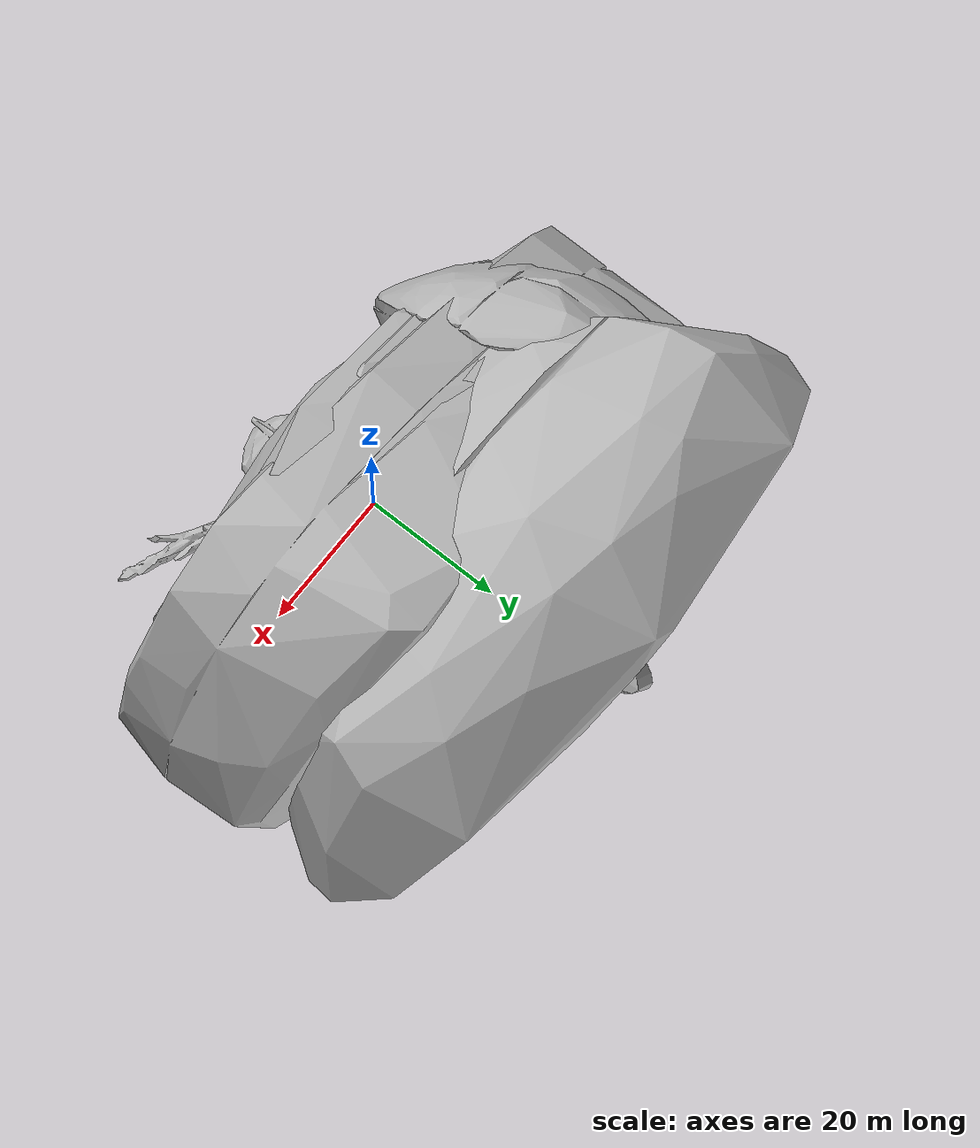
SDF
<?xml version="1.0" ?>
<sdf version="1.6">
  <model name="neuromechfly_noLimits">
    <pose>0.0 0.0 0.0 0.0 -0.0 0.0</pose>
    <link name="A1A2">
      <pose>-0.3096564710140228 -6.095955882301496e-07 0.9105792045593262 0.0 -0.0 0.0</pose>
      <inertial>
        <pose>-0.2144249677658081 -6.603514339076355e-05 0.07071342319250107 1.2543755769729614 -0.000939343823119998 -1.570754051208496</pose>
        <mass>8.571491383277525e-05</mass>
        <inertia>
          <ixx>5.379007258257524e-06</ixx>
          <ixy>-2.7172143083138003e-10</ixy>
          <ixz>-4.016699799635996e-07</ixz>
          <iyy>2.8840520398898414e-06</iyy>
          <iyz>1.2978086881476767e-09</iyz>
          <izz>4.283754254534721e-06</izz>
        </inertia>
      </inertial>
      <visual name="A1A2_visual">
        <pose>-2.3841858265427618e-08 -4.547473576627277e-14 -9.536743306171047e-08 0.0 -0.0 0.0</pose>
        <geometry>
          <mesh>
            <uri>../meshes/stl/A1A2.stl</uri>
            <scale>1000.0 1000.0 1000.0</scale>
          </mesh>
        </geometry>
        <material/>
      </visual>
    </link>
    <link name="A3">
      <pose>-0.666130006313324 -6.225838546924933e-07 0.9098724126815796 0.0 -0.2617993950843811 0.0</pose>
      <inertial>
        <pose>-0.05987601354718208 -6.470004882430658e-05 -0.02268083207309246 1.4835656881332397 -0.00017276499420404434 -1.5708097219467163</pose>
        <mass>0.00010704018580061077</mass>
        <inertia>
          <ixx>8.996426496899934e-06</ixx>
          <ixy>-1.0189078085903943e-10</ixy>
          <ixz>-2.182086660608849e-07</ixz>
          <iyy>4.18077287566254e-06</iyy>
          <iyz>4.0700063622846777e-10</iyz>
          <izz>6.520348442338967e-06</izz>
        </inertia>
      </inertial>
      <visual name="A3_visual">
        <pose>9.536743306171047e-08 -4.547473576627277e-14 -1.1920928955078125e-07 0.0 4.882812731921149e-08 0.0</pose>
        <geometry>
          <mesh>
            <uri>../meshes/stl/A3.stl</uri>
            <scale>1000.0 1000.0 1000.0</scale>
          </mesh>
        </geometry>
        <material/>
      </visual>
    </link>
    <link name="A4">
      <pose>-0.8957121968269348 -6.236073204490822e-07 0.8487271070480347 0.0 -0.5235987901687622 0.0</pose>
      <inertial>
        <pose>-0.06720209121704102 -2.9355971491895616e-05 -0.017197847366333008 1.482974648475647 -1.8414959413348697e-05 -1.5708448886871338</pose>
        <mass>9.752435108452857e-05</mass>
        <inertia>
          <ixx>8.05161514355576e-06</ixx>
          <ixy>-2.350168474990703e-10</ixy>
          <ixz>-1.6058848411617763e-07</ixz>
          <iyy>3.257527734203393e-06</iyy>
          <iyz>6.270709172547439e-11</iyz>
          <izz>6.2418857754968594e-06</izz>
        </inertia>
      </inertial>
      <visual name="A4_visual">
        <pose>0.0 0.0 0.0 0.0 -0.0 0.0</pose>
        <geometry>
          <mesh>
            <uri>../meshes/stl/A4.stl</uri>
            <scale>1000.0 1000.0 1000.0</scale>
          </mesh>
        </geometry>
        <material/>
      </visual>
    </link>
    <link name="A5">
      <pose>-1.0812511444091797 -6.25780387508712e-07 0.7414974570274353 0.0 -0.7853980660438538 0.0</pose>
      <inertial>
        <pose>-0.08348398655653 2.2320235075312667e-05 -0.040628910064697266 -1.5880876779556274 -0.0006984898936934769 1.5705978870391846</pose>
        <mass>9.704450609731538e-05</mass>
        <inertia>
          <ixx>6.510006856983616e-06</ixx>
          <ixy>-6.353942720115236e-10</ixy>
          <ixz>2.510708473554063e-08</ixz>
          <iyy>3.3950607369438554e-06</iyy>
          <iyz>-1.1669246567412128e-09</iyz>
          <izz>5.0585773842176395e-06</izz>
        </inertia>
      </inertial>
      <visual name="A5_visual">
        <pose>9.536743306171047e-08 -4.547473576627277e-14 4.7683716530855236e-08 0.0 4.882812731921149e-08 0.0</pose>
        <geometry>
          <mesh>
            <uri>../meshes/stl/A5.stl</uri>
            <scale>1000.0 1000.0 1000.0</scale>
          </mesh>
        </geometry>
        <material/>
      </visual>
    </link>
    <link name="A6">
      <pose>-1.271146535873413 -6.225404263204837e-07 0.5523146390914917 0.0 -1.0471974611282349 0.0</pose>
      <inertial>
        <pose>-0.05385642126202583 1.0378301340097096e-05 -0.0347994826734066 -1.4778363704681396 0.0007478894549421966 1.570986270904541</pose>
        <mass>6.267604318477003e-05</mass>
        <inertia>
          <ixx>2.5686907519812623e-06</ixx>
          <ixy>7.637514399896898e-11</ixy>
          <ixz>-4.9756936064053624e-08</ixz>
          <iyy>1.97061699442684e-06</iyy>
          <iyz>4.215461293405398e-11</iyz>
          <izz>2.0396207514768214e-06</izz>
        </inertia>
      </inertial>
      <visual name="A6_visual">
        <pose>0.0 -9.094947153254554e-14 0.0 0.0 -0.0 0.0</pose>
        <geometry>
          <mesh>
            <uri>../meshes/stl/A6.stl</uri>
            <scale>1000.0 1000.0 1000.0</scale>
          </mesh>
        </geometry>
        <material/>
      </visual>
    </link>
    <link name="Haustellum">
      <pose>0.5039694905281067 0.0002346131223021075 0.9939287304878235 0.0 0.698131799697876 0.0</pose>
      <inertial>
        <pose>0.20060499012470245 0.004706569481641054 -0.00878372322767973 -0.014601889066398144 0.00142684206366539 -0.01821466162800789</pose>
        <mass>6.941066853014398e-06</mass>
        <inertia>
          <ixx>4.907255111440599e-08</ixx>
          <ixy>1.7929555828165396e-10</ixy>
          <ixz>4.998376081429952e-11</ixz>
          <iyy>5.8887346186315783e-08</iyy>
          <iyz>3.09533767001756e-10</iyz>
          <izz>8.014157063555477e-08</izz>
        </inertia>
      </inertial>
      <visual name="Haustellum_visual">
        <pose>7.152558367806705e-08 2.3283064712331658e-11 2.3841861818141297e-08 0.0 -0.0 0.0</pose>
        <geometry>
          <mesh>
            <uri>../meshes/stl/Haustellum.stl</uri>
            <scale>1000.0 1000.0 1000.0</scale>
          </mesh>
        </geometry>
        <material/>
      </visual>
    </link>
    <link name="Head">
      <pose>0.49792253971099854 -6.537505328196858e-07 1.2107712030410767 0.0 0.1745329350233078 0.0</pose>
      <inertial>
        <pose>0.20209117233753204 -0.0043840003199875355 0.043947745114564896 -1.4147186279296875 -0.10165788233280182 1.612613320350647</pose>
        <mass>8.113157308044636e-05</mass>
        <inertia>
          <ixx>3.916686083637349e-06</ixx>
          <ixy>5.496640594677064e-08</ixy>
          <ixz>-1.355155214169488e-07</ixz>
          <iyy>2.937974490210881e-06</iyy>
          <iyz>-1.954467052189715e-08</iyz>
          <izz>3.069572001355821e-06</izz>
        </inertia>
      </inertial>
      <visual name="Head_visual">
        <pose>-9.536743306171047e-08 -1.364242106869501e-13 -2.3841858265427618e-08 0.0 -1.2207031829802872e-08 0.0</pose>
        <geometry>
          <mesh>
            <uri>../meshes/stl/Head.stl</uri>
            <scale>1000.0 1000.0 1000.0</scale>
          </mesh>
        </geometry>
        <material/>
      </visual>
    </link>
    <link name="Head_roll">
      <pose>0.4979226887226105 -6.537503054460103e-07 1.2107712030410767 0.0 -0.0 0.0</pose>
      <inertial>
        <pose>-4.7683716530855236e-08 -4.547473576627277e-14 -9.536743306171047e-08 -0.0 -0.0 0.0</pose>
        <mass>0.0</mass>
        <inertia>
          <ixx>0.0</ixx>
          <ixy>0.0</ixy>
          <ixz>0.0</ixz>
          <iyy>0.0</iyy>
          <iyz>0.0</iyz>
          <izz>0.0</izz>
        </inertia>
      </inertial>
    </link>
    <link name="Head_yaw">
      <pose>0.4979226291179657 -6.53750419132848e-07 1.2107712030410767 0.0 -0.0 0.0</pose>
      <inertial>
        <pose>0.0 -9.094947153254554e-14 -9.536743306171047e-08 -0.0 -0.0 0.0</pose>
        <mass>0.0</mass>
        <inertia>
          <ixx>0.0</ixx>
          <ixy>0.0</ixy>
          <ixz>0.0</ixz>
          <iyy>0.0</iyy>
          <iyz>0.0</iyz>
          <izz>0.0</izz>
        </inertia>
      </inertial>
    </link>
    <link name="LAntenna">
      <pose>0.9482773542404175 0.06690007448196411 1.273026466369629 0.5759586095809937 0.1745329350233078 0.0</pose>
      <inertial>
        <pose>0.05091390758752823 0.013138915412127972 -0.11156067997217178 -0.00021535124687943608 -1.7195219993591309 -2.814128875732422</pose>
        <mass>1.7777389383760332e-06</mass>
        <inertia>
          <ixx>1.2132654283335043e-08</ixx>
          <ixy>6.34643864390147e-10</ixy>
          <ixz>-1.0707396219956799e-09</ixz>
          <iyy>1.0481508781908762e-08</iyy>
          <iyz>-3.6379731017516985e-10</iyz>
          <izz>4.970367756570775e-09</izz>
        </inertia>
      </inertial>
      <visual name="LAntenna_visual">
        <pose>-9.536743306171047e-08 8.344650836988876e-08 1.3113022134803032e-07 0.0 1.2207031829802872e-08 6.103516358990646e-09</pose>
        <geometry>
          <mesh>
            <uri>../meshes/stl/LAntenna.stl</uri>
            <scale>1000.0 1000.0 1000.0</scale>
          </mesh>
        </geometry>
        <material/>
      </visual>
    </link>
    <link name="LEye">
      <pose>0.7419559359550476 -5.636523496832524e-07 1.258327603340149 0.0 0.1745329350233078 0.0</pose>
      <inertial>
        <pose>-0.00703806895762682 0.3009641766548157 -0.02373889647424221 -1.0532300472259521 -1.397886872291565 -0.1070028766989708</pose>
        <mass>9.502325241495403e-06</mass>
        <inertia>
          <ixx>1.3114464866873867e-07</ixx>
          <ixy>-2.390665136022388e-08</ixy>
          <ixz>-8.179075815846679e-09</ixz>
          <iyy>1.7805336805296216e-07</iyy>
          <iyz>5.857114763037776e-09</iyz>
          <izz>8.81424038962953e-08</izz>
        </inertia>
      </inertial>
      <visual name="LEye_visual">
        <pose>-4.7683716530855236e-08 -4.547473576627277e-14 -1.1920929132713809e-08 0.0 -1.2207031829802872e-08 0.0</pose>
        <geometry>
          <mesh>
            <uri>../meshes/stl/LEye.stl</uri>
            <scale>1000.0 1000.0 1000.0</scale>
          </mesh>
        </geometry>
        <material/>
      </visual>
    </link>
    <link name="LFCoxa">
      <pose>0.41799989342689514 0.2699994444847107 1.0799976587295532 0.0 -0.0 0.1745329350233078</pose>
      <inertial>
        <pose>0.002981042955070734 -0.03152111917734146 -0.2531244456768036 -0.7478164434432983 -1.6380294561386108 1.2891978025436401</pose>
        <mass>5.741707610995013e-06</mass>
        <inertia>
          <ixx>5.983418637183175e-08</ixx>
          <ixy>1.5355095860900972e-09</ixy>
          <ixz>9.568855434245275e-10</ixz>
          <iyy>5.79745744876736e-08</iyy>
          <iyz>2.8728611156529988e-09</iyz>
          <izz>1.4207714613335929e-08</izz>
        </inertia>
      </inertial>
      <visual name="LFCoxa_visual">
        <pose>4.7683716530855236e-08 1.1920929132713809e-08 0.0 0.0 -0.0 -1.2207031829802872e-08</pose>
        <geometry>
          <mesh>
            <uri>../meshes/stl/LFCoxa.stl</uri>
            <scale>1000.0 1000.0 1000.0</scale>
          </mesh>
        </geometry>
        <material/>
      </visual>
    </link>
    <link name="LFCoxa_roll">
      <pose>0.41799989342689514 0.2699994444847107 1.0799976587295532 0.0 -0.0 0.1745329350233078</pose>
      <inertial>
        <pose>4.7683716530855236e-08 1.1920929132713809e-08 0.0 -0.0 -0.0 0.0</pose>
        <mass>0.0</mass>
        <inertia>
          <ixx>0.0</ixx>
          <ixy>0.0</ixy>
          <ixz>0.0</ixz>
          <iyy>0.0</iyy>
          <iyz>0.0</iyz>
          <izz>0.0</izz>
        </inertia>
      </inertial>
    </link>
    <link name="LFCoxa_yaw">
      <pose>0.41799989342689514 0.2699994444847107 1.0799976587295532 0.0 -0.0 0.1745329350233078</pose>
      <inertial>
        <pose>4.7683716530855236e-08 1.1920929132713809e-08 0.0 -0.0 -0.0 0.0</pose>
        <mass>0.0</mass>
        <inertia>
          <ixx>0.0</ixx>
          <ixy>0.0</ixy>
          <ixz>0.0</ixz>
          <iyy>0.0</iyy>
          <iyz>0.0</iyz>
          <izz>0.0</izz>
        </inertia>
      </inertial>
    </link>
    <link name="LFFemur">
      <pose>0.41799989342689514 0.2699994444847107 0.6545163989067078 0.0 -0.0 0.1745329350233078</pose>
      <inertial>
        <pose>-0.01985769346356392 -0.0067473771050572395 -0.35944435000419617 0.058090921491384506 -1.6430429220199585 -2.0456981658935547</pose>
        <mass>7.992114412322805e-06</mass>
        <inertia>
          <ixx>2.7267902127637655e-07</ixx>
          <ixy>2.2529365411735334e-10</ixy>
          <ixz>-8.562267397467378e-09</ixz>
          <iyy>2.732996498121526e-07</iyy>
          <iyz>-1.6672479243976315e-08</iyz>
          <izz>1.5735837661850214e-08</izz>
        </inertia>
      </inertial>
      <visual name="LFFemur_visual">
        <pose>4.7683716530855236e-08 1.1920929132713809e-08 0.0 0.0 -0.0 -1.2207031829802872e-08</pose>
        <geometry>
          <mesh>
            <uri>../meshes/stl/LFFemur.stl</uri>
            <scale>1000.0 1000.0 1000.0</scale>
          </mesh>
        </geometry>
        <material/>
      </visual>
    </link>
    <link name="LFFemur_roll">
      <pose>0.41799989342689514 0.2699994444847107 0.6545163989067078 0.0 -0.0 0.1745329350233078</pose>
      <inertial>
        <pose>4.7683716530855236e-08 1.1920929132713809e-08 0.0 -0.0 -0.0 0.0</pose>
        <mass>0.0</mass>
        <inertia>
          <ixx>0.0</ixx>
          <ixy>0.0</ixy>
          <ixz>0.0</ixz>
          <iyy>0.0</iyy>
          <iyz>0.0</iyz>
          <izz>0.0</izz>
        </inertia>
      </inertial>
    </link>
    <link name="LFTarsus1">
      <pose>0.41799989342689514 0.2699994444847107 -0.5691056251525879 0.0 -0.6806784272193909 0.1745329201221466</pose>
      <inertial>
        <pose>-0.004590319935232401 -0.009428751654922962 -0.12341514974832535 2.432598352432251 -1.5347647666931152 -0.2797257900238037</pose>
        <mass>5.902334137063546e-07</mass>
        <inertia>
          <ixx>2.6619196564244832e-09</ixx>
          <ixy>-6.696196350980393e-12</ixy>
          <ixz>-8.499819284680847e-11</ixz>
          <iyy>2.671119021702012e-09</iyy>
          <iyz>2.4720518054378474e-11</iyz>
          <izz>2.137105482392998e-10</izz>
        </inertia>
      </inertial>
      <collision name="LFTarsus1_collision">
        <pose>0.0 1.1920929132713809e-08 -7.152556946721234e-08 0.0 -4.882813087192517e-08 1.5870162073383653e-08</pose>
        <geometry>
          <mesh>
            <uri>../meshes/stl/LFTarsus1.stl</uri>
            <scale>1000.0 1000.0 1000.0</scale>
          </mesh>
        </geometry>
      </collision>
      <visual name="LFTarsus1_visual">
        <pose>0.0 1.1920929132713809e-08 -7.152556946721234e-08 0.0 -4.882813087192517e-08 1.5870162073383653e-08</pose>
        <geometry>
          <mesh>
            <uri>../meshes/stl/LFTarsus1.stl</uri>
            <scale>1000.0 1000.0 1000.0</scale>
          </mesh>
        </geometry>
        <material/>
      </visual>
    </link>
    <link name="LFTarsus2">
      <pose>0.5577661991119385 0.29464399814605713 -0.7443650960922241 0.0 -0.6806784272193909 0.1745329201221466</pose>
      <inertial>
        <pose>-0.001288890722207725 -0.00532267102971673 -0.08914288878440857 -2.318387508392334 1.520503282546997 0.06142140552401543</pose>
        <mass>2.658976343874435e-07</mass>
        <inertia>
          <ixx>5.103329322322616e-10</ixx>
          <ixy>-4.652931733921339e-12</ixy>
          <ixz>2.2319235150477887e-11</ixz>
          <iyy>5.110168665053002e-10</iyy>
          <iyz>1.141795723786161e-12</iyz>
          <izz>6.692566660715184e-11</izz>
        </inertia>
      </inertial>
      <collision name="LFTarsus2_collision">
        <pose>0.0 3.5762788286319847e-08 7.152556946721234e-08 0.0 -4.882813087192517e-08 1.5870162073383653e-08</pose>
        <geometry>
          <mesh>
            <uri>../meshes/stl/LFTarsus2.stl</uri>
            <scale>1000.0 1000.0 1000.0</scale>
          </mesh>
        </geometry>
      </collision>
      <visual name="LFTarsus2_visual">
        <pose>0.0 3.5762788286319847e-08 7.152556946721234e-08 0.0 -4.882813087192517e-08 1.5870162073383653e-08</pose>
        <geometry>
          <mesh>
            <uri>../meshes/stl/LFTarsus2.stl</uri>
            <scale>1000.0 1000.0 1000.0</scale>
          </mesh>
        </geometry>
        <material/>
      </visual>
    </link>
    <link name="LFTarsus3">
      <pose>0.6530038714408875 0.3114369511604309 -0.8637880086898804 0.0 -0.6806784272193909 0.1745329201221466</pose>
      <inertial>
        <pose>-0.0010801791213452816 -0.0034542083740234375 -0.05935239419341087 0.3327091634273529 1.6532691717147827 2.7066781520843506</pose>
        <mass>1.5048445915428457e-07</mass>
        <inertia>
          <ixx>1.2943798832106454e-10</ixx>
          <ixy>-1.636254884174268e-12</ixy>
          <ixz>7.384017845364119e-12</ixz>
          <iyy>1.2973339477855396e-10</iyy>
          <iyz>-3.5369691091179722e-12</iyz>
          <izz>3.237591364465404e-11</izz>
        </inertia>
      </inertial>
      <collision name="LFTarsus3_collision">
        <pose>4.768370942542788e-08 2.3841858265427618e-08 -4.768371297814156e-08 0.0 -4.882813087192517e-08 1.5870162073383653e-08</pose>
        <geometry>
          <mesh>
            <uri>../meshes/stl/LFTarsus3.stl</uri>
            <scale>1000.0 1000.0 1000.0</scale>
          </mesh>
        </geometry>
      </collision>
      <visual name="LFTarsus3_visual">
        <pose>4.768370942542788e-08 2.3841858265427618e-08 -4.768371297814156e-08 0.0 -4.882813087192517e-08 1.5870162073383653e-08</pose>
        <geometry>
          <mesh>
            <uri>../meshes/stl/LFTarsus3.stl</uri>
            <scale>1000.0 1000.0 1000.0</scale>
          </mesh>
        </geometry>
        <material/>
      </visual>
    </link>
    <link name="LFTarsus4">
      <pose>0.7140486836433411 0.3222007751464844 -0.9403349161148071 0.0 -0.6806784272193909 0.1745329201221466</pose>
      <inertial>
        <pose>0.00086970318807289 -0.0014729738468304276 -0.049973007291555405 -2.727588176727295 1.487036108970642 -0.4085111916065216</pose>
        <mass>1.1769954786975934e-07</mass>
        <inertia>
          <ixx>7.574844946658414e-11</ixx>
          <ixy>-1.1218003527775303e-12</ixy>
          <ixz>4.142658799359131e-12</ixz>
          <iyy>7.619289827697055e-11</iyy>
          <iyz>-1.8782525110208446e-12</iyz>
          <izz>2.2848746233067172e-11</izz>
        </inertia>
      </inertial>
      <collision name="LFTarsus4_collision">
        <pose>0.0 -1.1920929132713809e-08 -4.768371297814156e-08 0.0 -4.882813087192517e-08 1.5870162073383653e-08</pose>
        <geometry>
          <mesh>
            <uri>../meshes/stl/LFTarsus4.stl</uri>
            <scale>1000.0 1000.0 1000.0</scale>
          </mesh>
        </geometry>
      </collision>
      <visual name="LFTarsus4_visual">
        <pose>0.0 -1.1920929132713809e-08 -4.768371297814156e-08 0.0 -4.882813087192517e-08 1.5870162073383653e-08</pose>
        <geometry>
          <mesh>
            <uri>../meshes/stl/LFTarsus4.stl</uri>
            <scale>1000.0 1000.0 1000.0</scale>
          </mesh>
        </geometry>
        <material/>
      </visual>
    </link>
    <link name="LFTarsus5">
      <pose>0.7679671049118042 0.33170804381370544 -1.0079456567764282 0.0 -0.6806784272193909 0.1745329201221466</pose>
      <inertial>
        <pose>0.002577590523287654 -0.00088839529780671 -0.05205821618437767 1.7842026948928833 1.4631301164627075 -0.10700467973947525</pose>
        <mass>1.4544444513923852e-07</mass>
        <inertia>
          <ixx>1.135124894575874e-10</ixx>
          <ixy>-5.371669362193046e-13</ixy>
          <ixz>8.61959329236233e-12</ixz>
          <iyy>1.203871149303067e-10</iyy>
          <iyz>-1.0622825672702412e-12</iyz>
          <izz>3.4301165518026506e-11</izz>
        </inertia>
      </inertial>
      <collision name="LFTarsus5_collision">
        <pose>4.768370942542788e-08 0.0 -4.768371297814156e-08 0.0 -4.882813087192517e-08 1.5870162073383653e-08</pose>
        <geometry>
          <mesh>
            <uri>../meshes/stl/LFTarsus5.stl</uri>
            <scale>1000.0 1000.0 1000.0</scale>
          </mesh>
        </geometry>
      </collision>
      <visual name="LFTarsus5_visual">
        <pose>4.768370942542788e-08 0.0 -4.768371297814156e-08 0.0 -4.882813087192517e-08 1.5870162073383653e-08</pose>
        <geometry>
          <mesh>
            <uri>../meshes/stl/LFTarsus5.stl</uri>
            <scale>1000.0 1000.0 1000.0</scale>
          </mesh>
        </geometry>
        <material/>
      </visual>
    </link>
    <link name="LFTibia">
      <pose>0.41799989342689514 0.2699994444847107 -0.05072354897856712 0.0 -0.0 0.1745329350233078</pose>
      <inertial>
        <pose>0.011397123336791992 -0.0035875679459422827 -0.2930237948894501 -0.1194225624203682 1.5173075199127197 0.8453858494758606</pose>
        <mass>2.6268343212263377e-06</mass>
        <inertia>
          <ixx>5.50390271997034e-08</ixx>
          <ixy>1.5267819432842367e-10</ixy>
          <ixz>1.8890251848431905e-09</ixz>
          <iyy>5.5191946361538317e-08</iyy>
          <iyz>2.1350840278172453e-09</iyz>
          <izz>2.18284819569887e-09</izz>
        </inertia>
      </inertial>
      <visual name="LFTibia_visual">
        <pose>4.7683716530855236e-08 1.1920929132713809e-08 0.0 0.0 -0.0 -1.2207031829802872e-08</pose>
        <geometry>
          <mesh>
            <uri>../meshes/stl/LFTibia.stl</uri>
            <scale>1000.0 1000.0 1000.0</scale>
          </mesh>
        </geometry>
        <material/>
      </visual>
    </link>
    <link name="LHaltere">
      <pose>-0.2589678168296814 0.21355578303337097 0.9370104670524597 0.0 -0.0 0.0</pose>
      <inertial>
        <pose>-0.008205438032746315 0.2060527801513672 -0.0006526947254315019 1.4957826137542725 0.005248593166470528 -1.5721955299377441</pose>
        <mass>1.4160896935430824e-06</mass>
        <inertia>
          <ixx>1.4020303628986903e-08</ixx>
          <ixy>-1.6711254076134715e-11</ixy>
          <ixz>-2.8079219660502452e-11</ixz>
          <iyy>1.9730319364747313e-09</iyy>
          <iyz>-6.1248840665395e-11</iyz>
          <izz>1.3649625794138886e-08</izz>
        </inertia>
      </inertial>
      <visual name="LHaltere_visual">
        <pose>-2.3841858265427618e-08 2.3841858265427618e-08 0.0 0.0 -0.0 0.0</pose>
        <geometry>
          <mesh>
            <uri>../meshes/stl/LHaltere.stl</uri>
            <scale>1000.0 1000.0 1000.0</scale>
          </mesh>
        </geometry>
        <material/>
      </visual>
    </link>
    <link name="LHaltere_roll">
      <pose>-0.2589678168296814 0.2135557234287262 0.9370104670524597 0.0 -0.0 0.0</pose>
      <inertial>
        <pose>-2.3841858265427618e-08 2.3841858265427618e-08 0.0 -0.0 -0.0 0.0</pose>
        <mass>0.0</mass>
        <inertia>
          <ixx>0.0</ixx>
          <ixy>0.0</ixy>
          <ixz>0.0</ixz>
          <iyy>0.0</iyy>
          <iyz>0.0</iyz>
          <izz>0.0</izz>
        </inertia>
      </inertial>
    </link>
    <link name="LHaltere_yaw">
      <pose>-0.2589678168296814 0.21355575323104858 0.9370104670524597 0.0 -0.0 0.0</pose>
      <inertial>
        <pose>-2.3841858265427618e-08 2.3841858265427618e-08 0.0 -0.0 -0.0 0.0</pose>
        <mass>0.0</mass>
        <inertia>
          <ixx>0.0</ixx>
          <ixy>0.0</ixy>
          <ixz>0.0</ixz>
          <iyy>0.0</iyy>
          <iyz>0.0</iyz>
          <izz>0.0</izz>
        </inertia>
      </inertial>
    </link>
    <link name="LHCoxa">
      <pose>-0.14771771430969238 0.08699285238981247 0.607223391532898 0.0 0.10821042954921722 0.0</pose>
      <inertial>
        <pose>-0.00381984724663198 0.020953847095370293 -0.10100870579481125 0.19215518236160278 1.2247357368469238 1.4062210321426392</pose>
        <mass>3.2548936150106453e-06</mass>
        <inertia>
          <ixx>1.350804012338567e-08</ixx>
          <ixy>-1.6370509791399278e-10</ixy>
          <ixz>2.639987688459687e-10</ixz>
          <iyy>1.4484483552670528e-08</iyy>
          <iyz>2.2778771682240345e-09</iyz>
          <izz>8.879176902911457e-09</izz>
        </inertia>
      </inertial>
      <visual name="LHCoxa_visual">
        <pose>-1.1920929132713809e-08 -5.9604645663569045e-09 2.6822091214739885e-08 0.0 -0.0 0.0</pose>
        <geometry>
          <mesh>
            <uri>../meshes/stl/LHCoxa.stl</uri>
            <scale>1000.0 1000.0 1000.0</scale>
          </mesh>
        </geometry>
        <material/>
      </visual>
    </link>
    <link name="LHCoxa_roll">
      <pose>-0.14771771430969238 0.08699285984039307 0.6072235703468323 0.060213852673769 0.10821042954921722 0.0</pose>
      <inertial>
        <pose>1.1920929132713809e-08 5.9604645663569045e-09 -1.0430812658057675e-08 -0.0 -0.0 0.0</pose>
        <mass>0.0</mass>
        <inertia>
          <ixx>0.0</ixx>
          <ixy>0.0</ixy>
          <ixz>0.0</ixz>
          <iyy>0.0</iyy>
          <iyz>0.0</iyz>
          <izz>0.0</izz>
        </inertia>
      </inertial>
    </link>
    <link name="LHCoxa_yaw">
      <pose>-0.14771771430969238 0.08699285984039307 0.6072234511375427 0.060213852673769 0.10821042954921722 0.0</pose>
      <inertial>
        <pose>3.5762788286319847e-08 1.1920929132713809e-08 3.725290298461914e-08 -0.0 -0.0 0.0</pose>
        <mass>0.0</mass>
        <inertia>
          <ixx>0.0</ixx>
          <ixy>0.0</ixy>
          <ixz>0.0</ixz>
          <iyy>0.0</iyy>
          <iyz>0.0</iyz>
          <izz>0.0</izz>
        </inertia>
      </inertial>
    </link>
    <link name="LHFemur">
      <pose>-0.16949017345905304 0.09876787662506104 0.40934833884239197 0.060213852673769 0.10821042954921722 0.0</pose>
      <inertial>
        <pose>0.03316855430603027 -0.018455779179930687 -0.43907609581947327 0.09182910621166229 1.5434627532958984 0.8837730884552002</pose>
        <mass>1.1113719808091789e-05</mass>
        <inertia>
          <ixx>5.240769260201016e-07</ixx>
          <ixy>3.451887877192935e-09</ixy>
          <ixz>8.697293494739268e-09</ixz>
          <iyy>5.240994330025576e-07</iyy>
          <iyz>1.0573373286421583e-08</iyz>
          <izz>2.7097994814382908e-08</izz>
        </inertia>
      </inertial>
      <visual name="LHFemur_visual">
        <pose>1.1920929132713809e-08 -1.1920929132713809e-08 -1.1920929132713809e-08 -6.103515470812226e-09 -1.2207031829802872e-08 7.629394893626795e-10</pose>
        <geometry>
          <mesh>
            <uri>../meshes/stl/LHFemur.stl</uri>
            <scale>1000.0 1000.0 1000.0</scale>
          </mesh>
        </geometry>
        <material/>
      </visual>
    </link>
    <link name="LHFemur_roll">
      <pose>-0.16949017345905304 0.09876789152622223 0.40934833884239197 0.060213852673769 0.10821042954921722 0.0</pose>
      <inertial>
        <pose>1.1920929132713809e-08 -5.9604645663569045e-09 -1.3411045607369942e-08 -0.0 -0.0 0.0</pose>
        <mass>0.0</mass>
        <inertia>
          <ixx>0.0</ixx>
          <ixy>0.0</ixy>
          <ixz>0.0</ixz>
          <iyy>0.0</iyy>
          <iyz>0.0</iyz>
          <izz>0.0</izz>
        </inertia>
      </inertial>
    </link>
    <link name="LHTarsus1">
      <pose>-0.3330475687980652 0.18928992748260498 -1.0998880863189697 0.07673919945955276 -0.675554096698761 -0.05455557256937027</pose>
      <inertial>
        <pose>-0.002593171549960971 0.0040600779466331005 -0.16763965785503387 -0.359566330909729 -1.5572956800460815 -0.6817010045051575</pose>
        <mass>1.3249969982172918e-06</mass>
        <inertia>
          <ixx>1.3948833895937138e-08</ixx>
          <ixy>-3.408937645724606e-11</ixy>
          <ixz>-1.3881187401653182e-10</ixz>
          <iyy>1.3855442366983524e-08</iyy>
          <iyz>1.1197135410054028e-10</iyz>
          <izz>7.38346273473165e-10</izz>
        </inertia>
      </inertial>
      <collision name="LHTarsus1_collision">
        <pose>0.0 -1.1920929132713809e-08 -9.536744016713783e-08 3.051757957450718e-09 -0.0 3.051757957450718e-09</pose>
        <geometry>
          <mesh>
            <uri>../meshes/stl/LHTarsus1.stl</uri>
            <scale>1000.0 1000.0 1000.0</scale>
          </mesh>
        </geometry>
      </collision>
      <visual name="LHTarsus1_visual">
        <pose>0.0 -1.1920929132713809e-08 -9.536744016713783e-08 3.051757957450718e-09 -0.0 3.051757957450718e-09</pose>
        <geometry>
          <mesh>
            <uri>../meshes/stl/LHTarsus1.stl</uri>
            <scale>1000.0 1000.0 1000.0</scale>
          </mesh>
        </geometry>
        <material/>
      </visual>
    </link>
    <link name="LHTarsus2">
      <pose>-0.11201035976409912 0.2049466073513031 -1.374342441558838 0.07673919945955276 -0.675554096698761 -0.05455557256937027</pose>
      <inertial>
        <pose>-0.001334244036115706 0.0022927522659301758 -0.09138837456703186 1.0428829193115234 1.5333383083343506 -0.9173977971076965</pose>
        <mass>4.465595046515482e-07</mass>
        <inertia>
          <ixx>1.2421568618269873e-09</ixx>
          <ixy>3.9195335774079074e-12</ixy>
          <ixz>2.460386567916838e-11</ixz>
          <iyy>1.248205629659075e-09</iyy>
          <iyz>-3.238046634512226e-11</iyz>
          <izz>1.5854710744795977e-10</izz>
        </inertia>
      </inertial>
      <collision name="LHTarsus2_collision">
        <pose>4.7683716530855236e-08 0.0 -1.5497208494252845e-07 3.051757957450718e-09 -0.0 3.051757957450718e-09</pose>
        <geometry>
          <mesh>
            <uri>../meshes/stl/LHTarsus2.stl</uri>
            <scale>1000.0 1000.0 1000.0</scale>
          </mesh>
        </geometry>
      </collision>
      <visual name="LHTarsus2_visual">
        <pose>4.7683716530855236e-08 0.0 -1.5497208494252845e-07 3.051757957450718e-09 -0.0 3.051757957450718e-09</pose>
        <geometry>
          <mesh>
            <uri>../meshes/stl/LHTarsus2.stl</uri>
            <scale>1000.0 1000.0 1000.0</scale>
          </mesh>
        </geometry>
        <material/>
      </visual>
    </link>
    <link name="LHTarsus3">
      <pose>-0.0022886991500854492 0.21143046021461487 -1.5105903148651123 0.07673919945955276 -0.675554096698761 -0.05455557256937027</pose>
      <inertial>
        <pose>-0.004137060139328241 0.003209757851436734 -0.04882475733757019 2.0993337631225586 -1.5832905769348145 -0.9562723636627197</pose>
        <mass>1.717215492644912e-07</mass>
        <inertia>
          <ixx>1.5704891128179778e-10</ixx>
          <ixy>1.5793452052281098e-12</ixy>
          <ixz>8.109874817632491e-13</ixz>
          <iyy>1.597724065762652e-10</iyy>
          <iyz>-1.1885304928094258e-12</iyz>
          <izz>4.22558145229839e-11</izz>
        </inertia>
      </inertial>
      <collision name="LHTarsus3_collision">
        <pose>2.1606684441621837e-08 0.0 -1.6093255794658035e-07 3.051757957450718e-09 -0.0 3.051757957450718e-09</pose>
        <geometry>
          <mesh>
            <uri>../meshes/stl/LHTarsus3.stl</uri>
            <scale>1000.0 1000.0 1000.0</scale>
          </mesh>
        </geometry>
      </collision>
      <visual name="LHTarsus3_visual">
        <pose>2.1606684441621837e-08 0.0 -1.6093255794658035e-07 3.051757957450718e-09 -0.0 3.051757957450718e-09</pose>
        <geometry>
          <mesh>
            <uri>../meshes/stl/LHTarsus3.stl</uri>
            <scale>1000.0 1000.0 1000.0</scale>
          </mesh>
        </geometry>
        <material/>
      </visual>
    </link>
    <link name="LHTarsus4">
      <pose>0.05833400785923004 0.21650132536888123 -1.585774302482605 0.07673919945955276 -0.675554096698761 -0.05455557256937027</pose>
      <inertial>
        <pose>-5.06639494801675e-08 -2.3841858265427618e-08 -8.344650836988876e-08 2.372253894805908 1.4789937734603882 -0.4670957624912262</pose>
        <mass>1.1443416496255567e-07</mass>
        <inertia>
          <ixx>2.4683293542298094e-10</ixx>
          <ixy>9.952485385943712e-15</ixy>
          <ixz>1.827232963853714e-11</ixz>
          <iyy>2.4985275489620366e-10</iyy>
          <iyz>-9.339634542772557e-12</iyz>
          <izz>2.642573729500649e-11</izz>
        </inertia>
      </inertial>
      <collision name="LHTarsus4_collision">
        <pose>-5.06639494801675e-08 -2.3841858265427618e-08 -8.344650836988876e-08 3.051757957450718e-09 -0.0 3.051757957450718e-09</pose>
        <geometry>
          <mesh>
            <uri>../meshes/stl/LHTarsus4.stl</uri>
            <scale>1000.0 1000.0 1000.0</scale>
          </mesh>
        </geometry>
      </collision>
      <visual name="LHTarsus4_visual">
        <pose>-5.06639494801675e-08 -2.3841858265427618e-08 -8.344650836988876e-08 3.051757957450718e-09 -0.0 3.051757957450718e-09</pose>
        <geometry>
          <mesh>
            <uri>../meshes/stl/LHTarsus4.stl</uri>
            <scale>1000.0 1000.0 1000.0</scale>
          </mesh>
        </geometry>
        <material/>
      </visual>
    </link>
    <link name="LHTarsus5">
      <pose>0.1043313518166542 0.21936455368995667 -1.642780065536499 0.07673919945955276 -0.675554096698761 -0.05455557256937027</pose>
      <inertial>
        <pose>-0.0017647863132879138 -0.00035610198392532766 -0.052608758211135864 -1.1455315351486206 -1.640228033065796 0.28557726740837097</pose>
        <mass>1.5831647994397422e-07</mass>
        <inertia>
          <ixx>1.275534557952797e-10</ixx>
          <ixy>1.0387493793363336e-12</ixy>
          <ixz>5.673485524053406e-12</ixz>
          <iyy>1.3596468492812532e-10</iyy>
          <iyz>1.8938777007182306e-12</iyz>
          <izz>4.324883583492056e-11</izz>
        </inertia>
      </inertial>
      <collision name="LHTarsus5_collision">
        <pose>1.7881394143159923e-08 -2.3841858265427618e-08 -1.6093255794658035e-07 3.051757957450718e-09 -0.0 3.051757957450718e-09</pose>
        <geometry>
          <mesh>
            <uri>../meshes/stl/LHTarsus5.stl</uri>
            <scale>1000.0 1000.0 1000.0</scale>
          </mesh>
        </geometry>
      </collision>
      <visual name="LHTarsus5_visual">
        <pose>1.7881394143159923e-08 -2.3841858265427618e-08 -1.6093255794658035e-07 3.051757957450718e-09 -0.0 3.051757957450718e-09</pose>
        <geometry>
          <mesh>
            <uri>../meshes/stl/LHTarsus5.stl</uri>
            <scale>1000.0 1000.0 1000.0</scale>
          </mesh>
        </geometry>
        <material/>
      </visual>
    </link>
    <link name="LHTibia">
      <pose>-0.2595152258872986 0.14873261749744415 -0.4206034541130066 0.060213852673769 0.10821042954921722 0.0</pose>
      <inertial>
        <pose>0.02332770824432373 -0.01545649766921997 -0.41772204637527466 -2.3637619018554688 -1.6249594688415527 -0.22312745451927185</pose>
        <mass>4.280437218327039e-06</mass>
        <inertia>
          <ixx>1.36571973333874e-07</ixx>
          <ixy>-3.589734864313778e-10</ixy>
          <ixz>6.984979984449975e-09</ixz>
          <iyy>1.373299267463762e-07</iyy>
          <iyz>-1.6120199397614828e-09</iyz>
          <izz>4.931242386774536e-09</izz>
        </inertia>
      </inertial>
      <visual name="LHTibia_visual">
        <pose>2.3841858265427618e-08 0.0 4.470348358154297e-08 -6.103515470812226e-09 -1.2207031829802872e-08 7.629394893626795e-10</pose>
        <geometry>
          <mesh>
            <uri>../meshes/stl/LHTibia.stl</uri>
            <scale>1000.0 1000.0 1000.0</scale>
          </mesh>
        </geometry>
        <material/>
      </visual>
    </link>
    <link name="LMCoxa">
      <pose>0.06767542660236359 0.1249004602432251 0.6798476576805115 0.0 -0.0872664600610733 0.0</pose>
      <inertial>
        <pose>-0.0013410926330834627 0.004880380816757679 -0.07880973815917969 -0.033913396298885345 -1.0169373750686646 -1.6626429557800293</pose>
        <mass>3.295969018637448e-06</mass>
        <inertia>
          <ixx>1.613857024264124e-08</ixx>
          <ixy>-5.2331361478733376e-11</ixy>
          <ixz>4.438624551510217e-10</ixz>
          <iyy>1.504033067194571e-08</iyy>
          <iyz>4.489648201221683e-09</iyz>
          <izz>1.0534992499367083e-08</izz>
        </inertia>
      </inertial>
      <visual name="LMCoxa_visual">
        <pose>5.9604645663569045e-09 -1.1920929132713809e-08 3.0174852838626975e-08 0.0 6.103515914901436e-09 0.0</pose>
        <geometry>
          <mesh>
            <uri>../meshes/stl/LMCoxa.stl</uri>
            <scale>1000.0 1000.0 1000.0</scale>
          </mesh>
        </geometry>
        <material/>
      </visual>
    </link>
    <link name="LMCoxa_roll">
      <pose>0.06767546385526657 0.1249004453420639 0.6798476576805115 0.13002702593803406 -0.0872664600610733 0.0</pose>
      <inertial>
        <pose>1.7881394143159923e-08 1.1920929132713809e-08 5.9604645663569045e-09 -0.0 -0.0 0.0</pose>
        <mass>0.0</mass>
        <inertia>
          <ixx>0.0</ixx>
          <ixy>0.0</ixy>
          <ixz>0.0</ixz>
          <iyy>0.0</iyy>
          <iyz>0.0</iyz>
          <izz>0.0</izz>
        </inertia>
      </inertial>
    </link>
    <link name="LMCoxa_yaw">
      <pose>0.06767543405294418 0.1249004453420639 0.6798476576805115 0.13002702593803406 -0.0872664600610733 0.0</pose>
      <inertial>
        <pose>1.1920929132713809e-08 1.1920929132713809e-08 8.940697071579962e-09 -0.0 -0.0 0.0</pose>
        <mass>0.0</mass>
        <inertia>
          <ixx>0.0</ixx>
          <ixy>0.0</ixy>
          <ixz>0.0</ixz>
          <iyy>0.0</iyy>
          <iyz>0.0</iyz>
          <izz>0.0</izz>
        </inertia>
      </inertial>
    </link>
    <link name="LMFemur">
      <pose>0.08313874900341034 0.1486310362815857 0.5006250143051147 0.13002702593803406 -0.0872664600610733 0.0</pose>
      <inertial>
        <pose>0.023515259847044945 0.002180075738579035 -0.40512463450431824 -0.8199150562286377 1.5611727237701416 1.1797511577606201</pose>
        <mass>8.23079136553737e-06</mass>
        <inertia>
          <ixx>4.0989546919810974e-07</ixx>
          <ixy>-1.0178035657241587e-10</ixy>
          <ixz>1.4528507113592936e-09</ixz>
          <iyy>4.100231084980835e-07</iyy>
          <iyz>3.526875993502687e-09</iyz>
          <izz>1.3630461220192824e-08</izz>
        </inertia>
      </inertial>
      <visual name="LMFemur_visual">
        <pose>5.9604645663569045e-09 1.1920929132713809e-08 1.1920929132713809e-08 1.2207031829802872e-08 -6.103515914901436e-09 7.629394893626795e-10</pose>
        <geometry>
          <mesh>
            <uri>../meshes/stl/LMFemur.stl</uri>
            <scale>1000.0 1000.0 1000.0</scale>
          </mesh>
        </geometry>
        <material/>
      </visual>
    </link>
    <link name="LMFemur_roll">
      <pose>0.08313874900341034 0.1486310362815857 0.5006250143051147 0.13002702593803406 -0.0872664600610733 0.0</pose>
      <inertial>
        <pose>5.9604645663569045e-09 1.1920929132713809e-08 1.1920929132713809e-08 -0.0 -0.0 0.0</pose>
        <mass>0.0</mass>
        <inertia>
          <ixx>0.0</ixx>
          <ixy>0.0</ixy>
          <ixz>0.0</ixz>
          <iyy>0.0</iyy>
          <iyz>0.0</iyz>
          <izz>0.0</izz>
        </inertia>
      </inertial>
    </link>
    <link name="LMTarsus1">
      <pose>0.2078336626291275 0.3378942012786865 -0.932561457157135 0.24800929427146912 -1.0166765451431274 -0.20069634914398193</pose>
      <inertial>
        <pose>-0.00750892236828804 0.00019421578326728195 -0.1536024510860443 -2.410893201828003 -1.5081813335418701 -0.324486643075943</pose>
        <mass>6.662969614149409e-07</mass>
        <inertia>
          <ixx>4.789018669521419e-09</ixx>
          <ixy>-1.0316838500437653e-11</ixy>
          <ixz>-2.7181504941603465e-10</ixz>
          <iyy>4.822226563942478e-09</iyy>
          <iyz>9.26397614655992e-11</iyz>
          <izz>2.3640331294254783e-10</izz>
        </inertia>
      </inertial>
      <collision name="LMTarsus1_collision">
        <pose>-3.5762788286319847e-08 0.0 4.7683723636282593e-08 -6.103516358990646e-09 4.882812376649781e-08 -1.2207029165267613e-08</pose>
        <geometry>
          <mesh>
            <uri>../meshes/stl/LMTarsus1.stl</uri>
            <scale>1000.0 1000.0 1000.0</scale>
          </mesh>
        </geometry>
      </collision>
      <visual name="LMTarsus1_visual">
        <pose>-3.5762788286319847e-08 0.0 4.7683723636282593e-08 -6.103516358990646e-09 4.882812376649781e-08 -1.2207029165267613e-08</pose>
        <geometry>
          <mesh>
            <uri>../meshes/stl/LMTarsus1.stl</uri>
            <scale>1000.0 1000.0 1000.0</scale>
          </mesh>
        </geometry>
        <material/>
      </visual>
    </link>
    <link name="LMTarsus2">
      <pose>0.4602377712726593 0.35980308055877686 -1.082383155822754 0.24800929427146912 -1.0166765451431274 -0.20069634914398193</pose>
      <inertial>
        <pose>-0.004910493269562721 0.0008204937330447137 -0.0791718140244484 -0.5143917202949524 -1.5483040809631348 -1.2652360200881958</pose>
        <mass>2.988951419617774e-07</mass>
        <inertia>
          <ixx>6.076981460248074e-10</ixx>
          <ixy>1.1809765506624864e-12</ixy>
          <ixz>-3.539365327898226e-12</ixz>
          <iyy>6.124552873374273e-10</iyy>
          <iyz>1.139464593442061e-11</iyz>
          <izz>8.12316436190037e-11</izz>
        </inertia>
      </inertial>
      <collision name="LMTarsus2_collision">
        <pose>-4.7683720083568915e-08 0.0 0.0 -6.103516358990646e-09 4.882812376649781e-08 -1.2207029165267613e-08</pose>
        <geometry>
          <mesh>
            <uri>../meshes/stl/LMTarsus2.stl</uri>
            <scale>1000.0 1000.0 1000.0</scale>
          </mesh>
        </geometry>
      </collision>
      <visual name="LMTarsus2_visual">
        <pose>-4.7683720083568915e-08 0.0 0.0 -6.103516358990646e-09 4.882812376649781e-08 -1.2207029165267613e-08</pose>
        <geometry>
          <mesh>
            <uri>../meshes/stl/LMTarsus2.stl</uri>
            <scale>1000.0 1000.0 1000.0</scale>
          </mesh>
        </geometry>
        <material/>
      </visual>
    </link>
    <link name="LMTarsus3">
      <pose>0.5965543389320374 0.37184661626815796 -1.1636625528335571 0.24800929427146912 -1.0166765451431274 -0.20069634914398193</pose>
      <inertial>
        <pose>-0.0020936967339366674 0.00206508650444448 -0.044653087854385376 -1.519486904144287 -1.6493254899978638 -0.2283748835325241</pose>
        <mass>1.49359671801039e-07</mass>
        <inertia>
          <ixx>1.1717508455759623e-10</ixx>
          <ixy>8.825598086039782e-13</ixy>
          <ixz>6.242686243253202e-12</ixz>
          <iyy>1.2009349778572921e-10</iyy>
          <iyz>-1.438987856164942e-12</iyz>
          <izz>3.602772507055522e-11</izz>
        </inertia>
      </inertial>
      <collision name="LMTarsus3_collision">
        <pose>-2.3841860041784457e-08 2.3841858265427618e-08 -9.536744727256519e-08 -6.103516358990646e-09 4.882812376649781e-08 -1.2207029165267613e-08</pose>
        <geometry>
          <mesh>
            <uri>../meshes/stl/LMTarsus3.stl</uri>
            <scale>1000.0 1000.0 1000.0</scale>
          </mesh>
        </geometry>
      </collision>
      <visual name="LMTarsus3_visual">
        <pose>-2.3841860041784457e-08 2.3841858265427618e-08 -9.536744727256519e-08 -6.103516358990646e-09 4.882812376649781e-08 -1.2207029165267613e-08</pose>
        <geometry>
          <mesh>
            <uri>../meshes/stl/LMTarsus3.stl</uri>
            <scale>1000.0 1000.0 1000.0</scale>
          </mesh>
        </geometry>
        <material/>
      </visual>
    </link>
    <link name="LMTarsus4">
      <pose>0.6735524535179138 0.3785530924797058 -1.2092543840408325 0.24800929427146912 -1.0166765451431274 -0.20069634914398193</pose>
      <inertial>
        <pose>-4.7683720083568915e-08 -2.3841858265427618e-08 4.7683723636282593e-08 -2.109145164489746 -1.6772009134292603 -0.2916592061519623</pose>
        <mass>8.690413245737014e-08</mass>
        <inertia>
          <ixx>1.210531784475736e-10</ixx>
          <ixy>-4.205742483408226e-14</ixy>
          <ixz>1.0531468623995063e-11</ixz>
          <iyy>1.2340492144548685e-10</iyy>
          <iyz>-3.237890546850215e-12</iyz>
          <izz>1.9293008159881107e-11</izz>
        </inertia>
      </inertial>
      <collision name="LMTarsus4_collision">
        <pose>-4.7683720083568915e-08 -2.3841858265427618e-08 4.7683723636282593e-08 -6.103516358990646e-09 4.882812376649781e-08 -1.2207029165267613e-08</pose>
        <geometry>
          <mesh>
            <uri>../meshes/stl/LMTarsus4.stl</uri>
            <scale>1000.0 1000.0 1000.0</scale>
          </mesh>
        </geometry>
      </collision>
      <visual name="LMTarsus4_visual">
        <pose>-4.7683720083568915e-08 -2.3841858265427618e-08 4.7683723636282593e-08 -6.103516358990646e-09 4.882812376649781e-08 -1.2207029165267613e-08</pose>
        <geometry>
          <mesh>
            <uri>../meshes/stl/LMTarsus4.stl</uri>
            <scale>1000.0 1000.0 1000.0</scale>
          </mesh>
        </geometry>
        <material/>
      </visual>
    </link>
    <link name="LMTarsus5">
      <pose>0.7278637290000916 0.38345015048980713 -1.241355299949646 0.24800929427146912 -1.0166765451431274 -0.20069634914398193</pose>
      <inertial>
        <pose>-0.0010362626053392887 -0.000547432922758162 -0.04305506497621536 1.4463443756103516 1.4698759317398071 0.145114928483963</pose>
        <mass>1.4474194312568478e-07</mass>
        <inertia>
          <ixx>1.163034938087531e-10</ixx>
          <ixy>-2.3589784652394145e-13</ixy>
          <ixz>8.24390216345855e-12</ixz>
          <iyy>1.2251731437552192e-10</iyy>
          <iyz>1.2726489418338513e-12</iyz>
          <izz>3.4839138473341044e-11</izz>
        </inertia>
      </inertial>
      <collision name="LMTarsus5_collision">
        <pose>0.0 0.0 -1.430511673561341e-07 -6.103516358990646e-09 4.882812376649781e-08 -1.2207029165267613e-08</pose>
        <geometry>
          <mesh>
            <uri>../meshes/stl/LMTarsus5.stl</uri>
            <scale>1000.0 1000.0 1000.0</scale>
          </mesh>
        </geometry>
      </collision>
      <visual name="LMTarsus5_visual">
        <pose>0.0 0.0 -1.430511673561341e-07 -6.103516358990646e-09 4.882812376649781e-08 -1.2207029165267613e-08</pose>
        <geometry>
          <mesh>
            <uri>../meshes/stl/LMTarsus5.stl</uri>
            <scale>1000.0 1000.0 1000.0</scale>
          </mesh>
        </geometry>
        <material/>
      </visual>
    </link>
    <link name="LMTibia">
      <pose>0.14989101886749268 0.2508229911327362 -0.27348142862319946 0.13002702593803406 -0.0872664600610733 0.0</pose>
      <inertial>
        <pose>0.022280216217041016 0.003726363182067871 -0.37377679347991943 0.33357036113739014 1.514025092124939 0.30270859599113464</pose>
        <mass>3.631542037586609e-06</mass>
        <inertia>
          <ixx>1.345167712576714e-07</ixx>
          <ixy>2.9286402925858677e-10</ixy>
          <ixz>7.144603790900179e-09</ixz>
          <iyy>1.3461153702722584e-07</iyy>
          <iyz>2.247245573385288e-09</iyz>
          <izz>3.332214283800136e-09</izz>
        </inertia>
      </inertial>
      <visual name="LMTibia_visual">
        <pose>0.0 0.0 5.9604645663569045e-09 1.2207031829802872e-08 -6.103515914901436e-09 7.629394893626795e-10</pose>
        <geometry>
          <mesh>
            <uri>../meshes/stl/LMTibia.stl</uri>
            <scale>1000.0 1000.0 1000.0</scale>
          </mesh>
        </geometry>
        <material/>
      </visual>
    </link>
    <link name="LWing">
      <pose>-0.091605544090271 0.3698323369026184 1.3241826295852661 -0.2967059314250946 -0.0 1.5707963705062866</pose>
      <inertial>
        <pose>-0.11281480640172958 1.0776903629302979 0.08102910965681076 0.023573826998472214 -0.05251652002334595 1.6804592609405518</pose>
        <mass>2.500079241447992e-06</mass>
        <inertia>
          <ixx>7.968332571849391e-07</ixx>
          <ixy>6.886744796609743e-08</ixy>
          <ixz>7.821732080410048e-10</ixz>
          <iyy>1.8077978855800485e-07</iyy>
          <iyz>-4.182696170877211e-08</iyz>
          <izz>9.635553787092022e-07</izz>
        </inertia>
      </inertial>
      <visual name="LWing_visual">
        <pose>4.7683716530855236e-08 -6.556511777944252e-08 5.960465188081798e-08 0.0 -0.0 -2.910383395667384e-15</pose>
        <geometry>
          <mesh>
            <uri>../meshes/stl/LWing.stl</uri>
            <scale>1000.0 1000.0 1000.0</scale>
          </mesh>
        </geometry>
        <material/>
      </visual>
    </link>
    <link name="LWing_roll">
      <pose>-0.091605544090271 0.3698323369026184 1.324182152748108 0.0 -0.0 1.5707963705062866</pose>
      <inertial>
        <pose>0.0 0.0 9.536743306171047e-08 -0.0 -0.0 0.0</pose>
        <mass>0.0</mass>
        <inertia>
          <ixx>0.0</ixx>
          <ixy>0.0</ixy>
          <ixz>0.0</ixz>
          <iyy>0.0</iyy>
          <iyz>0.0</iyz>
          <izz>0.0</izz>
        </inertia>
      </inertial>
    </link>
    <link name="LWing_yaw">
      <pose>-0.091605544090271 0.3698323369026184 1.324182391166687 -0.2967059314250946 -0.0 1.5707963705062866</pose>
      <inertial>
        <pose>4.7683716530855236e-08 -6.556511777944252e-08 5.960465188081798e-08 -0.0 -0.0 0.0</pose>
        <mass>0.0</mass>
        <inertia>
          <ixx>0.0</ixx>
          <ixy>0.0</ixy>
          <ixz>0.0</ixz>
          <iyy>0.0</iyy>
          <iyz>0.0</iyz>
          <izz>0.0</izz>
        </inertia>
      </inertial>
    </link>
    <link name="prismatic_support_1">
      <pose>0.0 0.0 0.0 0.0 -0.0 0.0</pose>
      <inertial>
        <pose>0.0 0.0 0.0 -0.0 -0.0 0.0</pose>
        <mass>0.0</mass>
        <inertia>
          <ixx>0.0</ixx>
          <ixy>0.0</ixy>
          <ixz>0.0</ixz>
          <iyy>0.0</iyy>
          <iyz>0.0</iyz>
          <izz>0.0</izz>
        </inertia>
      </inertial>
    </link>
    <link name="prismatic_support_2">
      <pose>0.0 0.0 0.0 0.0 -0.0 0.0</pose>
      <inertial>
        <pose>0.0 0.0 0.0 -0.0 -0.0 0.0</pose>
        <mass>0.0</mass>
        <inertia>
          <ixx>0.0</ixx>
          <ixy>0.0</ixy>
          <ixz>0.0</ixz>
          <iyy>0.0</iyy>
          <iyz>0.0</iyz>
          <izz>0.0</izz>
        </inertia>
      </inertial>
    </link>
    <link name="RAntenna">
      <pose>0.9481759667396545 -0.06800425052642822 1.2725653648376465 -0.5759586095809937 0.1745329350233078 0.0</pose>
      <inertial>
        <pose>0.050924208015203476 -0.013293791562318802 -0.11155541241168976 0.01825924590229988 -1.419149398803711 -0.3158183991909027</pose>
        <mass>1.7777381698425424e-06</mass>
        <inertia>
          <ixx>1.2118144852256564e-08</ixx>
          <ixy>-6.470039446583768e-10</ixy>
          <ixz>-1.0934780127445053e-09</ixz>
          <iyy>1.048746933313142e-08</iyy>
          <iyz>3.638498471065401e-10</iyz>
          <izz>4.978045946204023e-09</izz>
        </inertia>
      </inertial>
      <visual name="RAntenna_visual">
        <pose>-9.536743306171047e-08 3.5762788286319847e-08 1.668930025289228e-07 0.0 1.2207031829802872e-08 -6.103516358990646e-09</pose>
        <geometry>
          <mesh>
            <uri>../meshes/stl/RAntenna.stl</uri>
            <scale>1000.0 1000.0 1000.0</scale>
          </mesh>
        </geometry>
        <material/>
      </visual>
    </link>
    <link name="REye">
      <pose>0.7419559955596924 -5.634856279357336e-07 1.258327603340149 0.0 0.1745329350233078 0.0</pose>
      <inertial>
        <pose>-0.012887763790786266 -0.317592054605484 -0.030690742656588554 1.0171442031860352 -1.3079166412353516 0.1543324887752533</pose>
        <mass>8.241895909613487e-06</mass>
        <inertia>
          <ixx>1.1751616768767936e-07</ixx>
          <ixy>2.0157095834173952e-08</ixy>
          <ixz>-1.2295797136979536e-08</ixz>
          <iyy>1.624799495495446e-07</iyy>
          <iyz>-9.003112986527057e-09</iyz>
          <izz>7.805335340170162e-08</izz>
        </inertia>
      </inertial>
      <visual name="REye_visual">
        <pose>-4.7683716530855236e-08 0.0 -9.536743306171047e-08 0.0 -1.2207031829802872e-08 0.0</pose>
        <geometry>
          <mesh>
            <uri>../meshes/stl/REye.stl</uri>
            <scale>1000.0 1000.0 1000.0</scale>
          </mesh>
        </geometry>
        <material/>
      </visual>
    </link>
    <link name="RFCoxa">
      <pose>0.41799992322921753 -0.27000027894973755 1.0799976587295532 0.0 -0.0 -0.1745329350233078</pose>
      <inertial>
        <pose>0.0029808522667735815 0.03152226284146309 -0.25312432646751404 0.7478206157684326 -1.6380293369293213 -1.289201259613037</pose>
        <mass>5.741706163530321e-06</mass>
        <inertia>
          <ixx>5.983416911264356e-08</ixx>
          <ixy>-1.5355083040571808e-09</ixy>
          <ixz>9.56871277198453e-10</ixz>
          <iyy>5.79745586306428e-08</iyy>
          <iyz>-2.872861574361646e-09</iyz>
          <izz>1.4207707028825396e-08</izz>
        </inertia>
      </inertial>
      <visual name="RFCoxa_visual">
        <pose>0.0 5.960464477539063e-08 0.0 0.0 -0.0 1.2207031829802872e-08</pose>
        <geometry>
          <mesh>
            <uri>../meshes/stl/RFCoxa.stl</uri>
            <scale>1000.0 1000.0 1000.0</scale>
          </mesh>
        </geometry>
        <material/>
      </visual>
    </link>
    <link name="RFCoxa_roll">
      <pose>0.41799992322921753 -0.27000051736831665 1.0799976587295532 0.0 -0.0 -0.1745329350233078</pose>
      <inertial>
        <pose>0.0 9.536743306171047e-08 0.0 -0.0 -0.0 0.0</pose>
        <mass>0.0</mass>
        <inertia>
          <ixx>0.0</ixx>
          <ixy>0.0</ixy>
          <ixz>0.0</ixz>
          <iyy>0.0</iyy>
          <iyz>0.0</iyz>
          <izz>0.0</izz>
        </inertia>
      </inertial>
    </link>
    <link name="RFCoxa_yaw">
      <pose>0.41799992322921753 -0.2700003981590271 1.0799976587295532 0.0 -0.0 -0.1745329350233078</pose>
      <inertial>
        <pose>0.0 4.7683716530855236e-08 0.0 -0.0 -0.0 0.0</pose>
        <mass>0.0</mass>
        <inertia>
          <ixx>0.0</ixx>
          <ixy>0.0</ixy>
          <ixz>0.0</ixz>
          <iyy>0.0</iyy>
          <iyz>0.0</iyz>
          <izz>0.0</izz>
        </inertia>
      </inertial>
    </link>
    <link name="RFFemur">
      <pose>0.41799992322921753 -0.270000159740448 0.6545186638832092 0.0 -0.0 -0.1745329350233078</pose>
      <inertial>
        <pose>-0.01985769346356392 0.006748521234840155 -0.3594456613063812 0.07037395238876343 -1.6539647579193115 1.9682718515396118</pose>
        <mass>7.99213320458308e-06</mass>
        <inertia>
          <ixx>2.72696734586788e-07</ixx>
          <ixy>-3.118284866606571e-10</ixy>
          <ixz>-8.359438387289132e-09</ixz>
          <iyy>2.728445283155863e-07</iyy>
          <iyz>1.9876090547921418e-08</iyz>
          <izz>1.617812996347602e-08</izz>
        </inertia>
      </inertial>
      <visual name="RFFemur_visual">
        <pose>-4.7683716530855236e-08 5.960464477539063e-08 4.7683716530855236e-08 0.0 -0.0 1.2207031829802872e-08</pose>
        <geometry>
          <mesh>
            <uri>../meshes/stl/RFFemur.stl</uri>
            <scale>1000.0 1000.0 1000.0</scale>
          </mesh>
        </geometry>
        <material/>
      </visual>
    </link>
    <link name="RFFemur_roll">
      <pose>0.41799992322921753 -0.27000004053115845 0.6545187830924988 0.0 -0.0 -0.1745329350233078</pose>
      <inertial>
        <pose>0.0 5.960464477539063e-08 4.7683716530855236e-08 -0.0 -0.0 0.0</pose>
        <mass>0.0</mass>
        <inertia>
          <ixx>0.0</ixx>
          <ixy>0.0</ixy>
          <ixz>0.0</ixz>
          <iyy>0.0</iyy>
          <iyz>0.0</iyz>
          <izz>0.0</izz>
        </inertia>
      </inertial>
    </link>
    <link name="RFTarsus1">
      <pose>0.41799989342689514 -0.26999983191490173 -0.5691338777542114 0.0 -0.9075711965560913 -0.1745329350233078</pose>
      <inertial>
        <pose>-0.004590344615280628 0.009429908357560635 -0.12338633835315704 0.7089829444885254 -1.5347644090652466 0.2797349691390991</pose>
        <mass>5.902334030056455e-07</mass>
        <inertia>
          <ixx>2.661919493380233e-09</ixx>
          <ixy>6.696252541221297e-12</ixy>
          <ixz>-8.49988421563367e-11</ixz>
          <iyy>2.671118876236604e-09</iyy>
          <iyz>-2.4721904367683828e-11</iyz>
          <izz>2.1371061734877214e-10</izz>
        </inertia>
      </inertial>
      <collision name="RFTarsus1_collision">
        <pose>-4.7683716530855236e-08 1.1920929132713809e-08 7.152557657263969e-08 0.0 -4.882812376649781e-08 -9.173652948391009e-09</pose>
        <geometry>
          <mesh>
            <uri>../meshes/stl/RFTarsus1.stl</uri>
            <scale>1000.0 1000.0 1000.0</scale>
          </mesh>
        </geometry>
      </collision>
      <visual name="RFTarsus1_visual">
        <pose>-4.7683716530855236e-08 1.1920929132713809e-08 7.152557657263969e-08 0.0 -4.882812376649781e-08 -9.173652948391009e-09</pose>
        <geometry>
          <mesh>
            <uri>../meshes/stl/RFTarsus1.stl</uri>
            <scale>1000.0 1000.0 1000.0</scale>
          </mesh>
        </geometry>
        <material/>
      </visual>
    </link>
    <link name="RFTarsus2">
      <pose>0.5929410457611084 -0.3008466064929962 -0.7079213857650757 0.0 -0.9075711965560913 -0.1745329350233078</pose>
      <inertial>
        <pose>-0.0012890816433355212 0.0053238156251609325 -0.0892031192779541 -0.823215901851654 1.5205036401748657 -0.06143040582537651</pose>
        <mass>2.6589763376152175e-07</mass>
        <inertia>
          <ixx>5.103329473595504e-10</ixx>
          <ixy>4.6529193246102694e-12</ixy>
          <ixz>2.2319121199781353e-11</ixz>
          <iyy>5.110168673582965e-10</iyy>
          <iyz>-1.1420441148966488e-12</iyz>
          <izz>6.692565506745885e-11</izz>
        </inertia>
      </inertial>
      <collision name="RFTarsus2_collision">
        <pose>-4.7683716530855236e-08 2.3841858265427618e-08 1.4305115314527939e-07 0.0 -4.882812376649781e-08 -9.173652948391009e-09</pose>
        <geometry>
          <mesh>
            <uri>../meshes/stl/RFTarsus2.stl</uri>
            <scale>1000.0 1000.0 1000.0</scale>
          </mesh>
        </geometry>
      </collision>
      <visual name="RFTarsus2_visual">
        <pose>-4.7683716530855236e-08 2.3841858265427618e-08 1.4305115314527939e-07 0.0 -4.882812376649781e-08 -9.173652948391009e-09</pose>
        <geometry>
          <mesh>
            <uri>../meshes/stl/RFTarsus2.stl</uri>
            <scale>1000.0 1000.0 1000.0</scale>
          </mesh>
        </geometry>
        <material/>
      </visual>
    </link>
    <link name="RFTarsus3">
      <pose>0.7121999263763428 -0.32187509536743164 -0.8025339841842651 0.0 -0.9075711965560913 -0.1745329350233078</pose>
      <inertial>
        <pose>-0.001080369926057756 0.0034553171135485172 -0.05940503999590874 -0.3327125310897827 1.48832368850708 0.43491169810295105</pose>
        <mass>1.5048445801063186e-07</mass>
        <inertia>
          <ixx>1.2943799114767103e-10</ixx>
          <ixy>1.6362498656956743e-12</ixy>
          <ixz>7.383992388634351e-12</ixz>
          <iyy>1.2973339731991452e-10</iyy>
          <iyz>3.5369150183889013e-12</iyz>
          <izz>3.237590515384331e-11</izz>
        </inertia>
      </inertial>
      <collision name="RFTarsus3_collision">
        <pose>4.7683716530855236e-08 -1.1920929132713809e-08 -4.7683716530855236e-08 0.0 -4.882812376649781e-08 -9.173652948391009e-09</pose>
        <geometry>
          <mesh>
            <uri>../meshes/stl/RFTarsus3.stl</uri>
            <scale>1000.0 1000.0 1000.0</scale>
          </mesh>
        </geometry>
      </collision>
      <visual name="RFTarsus3_visual">
        <pose>4.7683716530855236e-08 -1.1920929132713809e-08 -4.7683716530855236e-08 0.0 -4.882812376649781e-08 -9.173652948391009e-09</pose>
        <geometry>
          <mesh>
            <uri>../meshes/stl/RFTarsus3.stl</uri>
            <scale>1000.0 1000.0 1000.0</scale>
          </mesh>
        </geometry>
        <material/>
      </visual>
    </link>
    <link name="RFTarsus4">
      <pose>0.7886413931846619 -0.33535370230674744 -0.8631777763366699 0.0 -0.9075711965560913 -0.1745329350233078</pose>
      <inertial>
        <pose>0.0008695602300576866 0.00147410633508116 -0.050020840018987656 -0.4140114486217499 1.4870364665985107 0.40850380063056946</pose>
        <mass>1.1769954845621714e-07</mass>
        <inertia>
          <ixx>7.574845212622345e-11</ixx>
          <ixy>1.1217974558331867e-12</ixy>
          <ixz>4.142645119773969e-12</ixz>
          <iyy>7.61929006021046e-11</iyy>
          <iyz>1.8782227223917356e-12</iyz>
          <izz>2.2848742197809424e-11</izz>
        </inertia>
      </inertial>
      <collision name="RFTarsus4_collision">
        <pose>4.7683716530855236e-08 1.1920929132713809e-08 0.0 0.0 -4.882812376649781e-08 -9.173652948391009e-09</pose>
        <geometry>
          <mesh>
            <uri>../meshes/stl/RFTarsus4.stl</uri>
            <scale>1000.0 1000.0 1000.0</scale>
          </mesh>
        </geometry>
      </collision>
      <visual name="RFTarsus4_visual">
        <pose>4.7683716530855236e-08 1.1920929132713809e-08 0.0 0.0 -4.882812376649781e-08 -9.173652948391009e-09</pose>
        <geometry>
          <mesh>
            <uri>../meshes/stl/RFTarsus4.stl</uri>
            <scale>1000.0 1000.0 1000.0</scale>
          </mesh>
        </geometry>
        <material/>
      </visual>
    </link>
    <link name="RFTarsus5">
      <pose>0.8561739325523376 -0.3472614288330078 -0.916753888130188 0.0 -0.9075711965560913 -0.1745329350233078</pose>
      <inertial>
        <pose>0.0025773048400878906 0.0008895277860574424 -0.05208325386047363 1.3573983907699585 1.4631305932998657 0.10699721425771713</pose>
        <mass>1.4544445851261665e-07</mass>
        <inertia>
          <ixx>1.1351250822278854e-10</ixx>
          <ixy>5.371606517909682e-13</ixy>
          <ixz>8.61956236424173e-12</ixz>
          <iyy>1.2038712906384415e-10</iyy>
          <iyz>1.0622193925558108e-12</iyz>
          <izz>3.430116323046479e-11</izz>
        </inertia>
      </inertial>
      <collision name="RFTarsus5_collision">
        <pose>0.0 2.3841858265427618e-08 -4.7683716530855236e-08 0.0 -4.882812376649781e-08 -9.173652948391009e-09</pose>
        <geometry>
          <mesh>
            <uri>../meshes/stl/RFTarsus5.stl</uri>
            <scale>1000.0 1000.0 1000.0</scale>
          </mesh>
        </geometry>
      </collision>
      <visual name="RFTarsus5_visual">
        <pose>0.0 2.3841858265427618e-08 -4.7683716530855236e-08 0.0 -4.882812376649781e-08 -9.173652948391009e-09</pose>
        <geometry>
          <mesh>
            <uri>../meshes/stl/RFTarsus5.stl</uri>
            <scale>1000.0 1000.0 1000.0</scale>
          </mesh>
        </geometry>
        <material/>
      </visual>
    </link>
    <link name="RFTibia">
      <pose>0.41799992322921753 -0.2699999213218689 -0.050721097737550735 0.0 -0.0 -0.1745329350233078</pose>
      <inertial>
        <pose>0.011396932415664196 0.0035887479316443205 -0.29302603006362915 0.11940953880548477 1.6242852210998535 2.296194314956665</pose>
        <mass>2.626834378398769e-06</mass>
        <inertia>
          <ixx>5.5039029499039883e-08</ixx>
          <ixy>-1.526786740402749e-10</ixy>
          <ixz>1.8890109702508788e-09</ixz>
          <iyy>5.519194524654044e-08</iyy>
          <iyz>-2.1351137781782823e-09</iyz>
          <izz>2.1828496369105125e-09</izz>
        </inertia>
      </inertial>
      <visual name="RFTibia_visual">
        <pose>-4.7683716530855236e-08 5.960464477539063e-08 0.0 0.0 -0.0 1.2207031829802872e-08</pose>
        <geometry>
          <mesh>
            <uri>../meshes/stl/RFTibia.stl</uri>
            <scale>1000.0 1000.0 1000.0</scale>
          </mesh>
        </geometry>
        <material/>
      </visual>
    </link>
    <link name="RHaltere">
      <pose>-0.2589678466320038 -0.2135571837425232 0.9370102286338806 0.0 -0.0 0.0</pose>
      <inertial>
        <pose>-0.007629299070686102 -0.20604589581489563 -0.002871227217838168 1.2210286855697632 -0.005481530446559191 -1.5712034702301025</pose>
        <mass>1.41608730082593e-06</mass>
        <inertia>
          <ixx>1.3978402491582015e-08</ixx>
          <ixy>-5.5496539257974766e-12</ixy>
          <ixz>-1.206051894354656e-10</ixz>
          <iyy>1.9730418168460516e-09</iyy>
          <iyz>6.428633454569222e-11</iyz>
          <izz>1.3691341329253386e-08</izz>
        </inertia>
      </inertial>
      <visual name="RHaltere_visual">
        <pose>-2.3841858265427618e-08 0.0 0.0 0.0 -0.0 0.0</pose>
        <geometry>
          <mesh>
            <uri>../meshes/stl/RHaltere.stl</uri>
            <scale>1000.0 1000.0 1000.0</scale>
          </mesh>
        </geometry>
        <material/>
      </visual>
    </link>
    <link name="RHaltere_roll">
      <pose>-0.25896772742271423 -0.21355724334716797 0.9370102286338806 0.0 -0.0 0.0</pose>
      <inertial>
        <pose>-4.7683716530855236e-08 2.3841858265427618e-08 0.0 -0.0 -0.0 0.0</pose>
        <mass>0.0</mass>
        <inertia>
          <ixx>0.0</ixx>
          <ixy>0.0</ixy>
          <ixz>0.0</ixz>
          <iyy>0.0</iyy>
          <iyz>0.0</iyz>
          <izz>0.0</izz>
        </inertia>
      </inertial>
    </link>
    <link name="RHaltere_yaw">
      <pose>-0.258967787027359 -0.21355721354484558 0.9370102286338806 0.0 -0.0 0.0</pose>
      <inertial>
        <pose>-4.7683716530855236e-08 2.3841858265427618e-08 0.0 -0.0 -0.0 0.0</pose>
        <mass>0.0</mass>
        <inertia>
          <ixx>0.0</ixx>
          <ixy>0.0</ixy>
          <ixz>0.0</ixz>
          <iyy>0.0</iyy>
          <iyz>0.0</iyz>
          <izz>0.0</izz>
        </inertia>
      </inertial>
    </link>
    <link name="RHCoxa">
      <pose>-0.1477178931236267 -0.08699406683444977 0.6072231531143188 0.0 0.1745329350233078 0.0</pose>
      <inertial>
        <pose>-0.0037281871773302555 -0.020860398188233376 -0.1010221466422081 -0.19146525859832764 1.9176486730575562 1.7328888177871704</pose>
        <mass>3.2548946367291556e-06</mass>
        <inertia>
          <ixx>1.3508895444032225e-08</ixx>
          <ixy>1.654774844295877e-10</ixy>
          <ixz>2.5922456853699946e-10</ixz>
          <iyy>1.4480297162125718e-08</iyy>
          <iyz>-2.2830629086425194e-09</iyz>
          <izz>8.882772581122752e-09</izz>
        </inertia>
      </inertial>
      <visual name="RHCoxa_visual">
        <pose>0.0 0.0 -1.1920929132713809e-08 0.0 -1.2207031829802872e-08 0.0</pose>
        <geometry>
          <mesh>
            <uri>../meshes/stl/RHCoxa.stl</uri>
            <scale>1000.0 1000.0 1000.0</scale>
          </mesh>
        </geometry>
        <material/>
      </visual>
    </link>
    <link name="RHCoxa_roll">
      <pose>-0.1477178931236267 -0.08699408918619156 0.6072229743003845 0.012915432453155518 0.1745329350233078 0.0</pose>
      <inertial>
        <pose>1.1920929132713809e-08 0.0 -5.364418242947977e-08 -0.0 -0.0 0.0</pose>
        <mass>0.0</mass>
        <inertia>
          <ixx>0.0</ixx>
          <ixy>0.0</ixy>
          <ixz>0.0</ixz>
          <iyy>0.0</iyy>
          <iyz>0.0</iyz>
          <izz>0.0</izz>
        </inertia>
      </inertial>
    </link>
    <link name="RHCoxa_yaw">
      <pose>-0.1477178931236267 -0.08699407428503036 0.6072230935096741 0.012915432453155518 0.1745329350233078 0.0</pose>
      <inertial>
        <pose>1.1920929132713809e-08 -5.960465454535324e-09 -1.01327898960335e-07 -0.0 -0.0 0.0</pose>
        <mass>0.0</mass>
        <inertia>
          <ixx>0.0</ixx>
          <ixy>0.0</ixy>
          <ixz>0.0</ixz>
          <iyy>0.0</iyy>
          <iyz>0.0</iyz>
          <izz>0.0</izz>
        </inertia>
      </inertial>
    </link>
    <link name="RHFemur">
      <pose>-0.18241950869560242 -0.08400145173072815 0.41087090969085693 0.012915432453155518 0.1745329350233078 0.0</pose>
      <inertial>
        <pose>0.033161189407110214 0.018143972381949425 -0.4390891492366791 -0.07705849409103394 1.597694754600525 2.2735729217529297</pose>
        <mass>1.1113711231749002e-05</mass>
        <inertia>
          <ixx>5.240827422201451e-07</ixx>
          <ixy>-3.4471113660241967e-09</ixy>
          <ixz>8.719731828423071e-09</ixz>
          <iyy>5.24104138833571e-07</iyy>
          <iyz>-1.0271105917466366e-08</iyz>
          <izz>2.708600536854334e-08</izz>
        </inertia>
      </inertial>
      <visual name="RHFemur_visual">
        <pose>-3.5762788286319847e-08 0.0 8.940697071579962e-09 -7.629392118069234e-10 1.2207031829802872e-08 0.0</pose>
        <geometry>
          <mesh>
            <uri>../meshes/stl/RHFemur.stl</uri>
            <scale>1000.0 1000.0 1000.0</scale>
          </mesh>
        </geometry>
        <material/>
      </visual>
    </link>
    <link name="RHFemur_roll">
      <pose>-0.18241950869560242 -0.08400145173072815 0.41087090969085693 0.012915432453155518 0.1745329350233078 0.0</pose>
      <inertial>
        <pose>-3.5762788286319847e-08 0.0 8.940697071579962e-09 -0.0 -0.0 0.0</pose>
        <mass>0.0</mass>
        <inertia>
          <ixx>0.0</ixx>
          <ixy>0.0</ixy>
          <ixz>0.0</ixz>
          <iyy>0.0</iyy>
          <iyz>0.0</iyz>
          <izz>0.0</izz>
        </inertia>
      </inertial>
    </link>
    <link name="RHTarsus1">
      <pose>-0.44665083289146423 -0.06386049091815948 -1.0866317749023438 0.01685222052037716 -0.7155004739761353 -0.013298438861966133</pose>
      <inertial>
        <pose>-0.0030509948264807463 -0.0029546741861850023 -0.1676488071680069 0.5316655039787292 -1.5582245588302612 0.3027391731739044</pose>
        <mass>1.3250065372293525e-06</mass>
        <inertia>
          <ixx>1.3895980951092814e-08</ixx>
          <ixy>5.7649647416818145e-11</ixy>
          <ixz>-1.5814732178418856e-10</ixz>
          <iyy>1.390914368810993e-08</iyy>
          <iyz>-5.0070029915928587e-11</iyz>
          <izz>7.380251977580928e-10</izz>
        </inertia>
      </inertial>
      <collision name="RHTarsus1_collision">
        <pose>9.536743306171047e-08 0.0 -7.152557657263969e-08 -7.629392118069234e-10 -0.0 -7.62939600384982e-10</pose>
        <geometry>
          <mesh>
            <uri>../meshes/stl/RHTarsus1.stl</uri>
            <scale>1000.0 1000.0 1000.0</scale>
          </mesh>
        </geometry>
      </collision>
      <visual name="RHTarsus1_visual">
        <pose>9.536743306171047e-08 0.0 -7.152557657263969e-08 -7.629392118069234e-10 -0.0 -7.62939600384982e-10</pose>
        <geometry>
          <mesh>
            <uri>../meshes/stl/RHTarsus1.stl</uri>
            <scale>1000.0 1000.0 1000.0</scale>
          </mesh>
        </geometry>
        <material/>
      </visual>
    </link>
    <link name="RHTarsus2">
      <pose>-0.21503621339797974 -0.06103786826133728 -1.3526667356491089 0.01685222052037716 -0.7155004739761353 -0.013298438861966133</pose>
      <inertial>
        <pose>-0.0011621474986895919 -0.0024351899046450853 -0.09136330336332321 -1.1477198600769043 1.5384025573730469 0.5718149542808533</pose>
        <mass>4.4655875421415463e-07</mass>
        <inertia>
          <ixx>1.2470445836855713e-09</ixx>
          <ixy>-4.81283578894369e-12</ixy>
          <ixz>2.961874361372959e-11</ixz>
          <iyy>1.2436939062143497e-09</iyy>
          <iyz>1.8925046940676516e-11</iyz>
          <izz>1.5816310328272482e-10</izz>
        </inertia>
      </inertial>
      <collision name="RHTarsus2_collision">
        <pose>3.5762788286319847e-08 -1.1920930909070648e-08 -4.7683720083568915e-08 -7.629392118069234e-10 -0.0 -7.62939600384982e-10</pose>
        <geometry>
          <mesh>
            <uri>../meshes/stl/RHTarsus2.stl</uri>
            <scale>1000.0 1000.0 1000.0</scale>
          </mesh>
        </geometry>
      </collision>
      <visual name="RHTarsus2_visual">
        <pose>3.5762788286319847e-08 -1.1920930909070648e-08 -4.7683720083568915e-08 -7.629392118069234e-10 -0.0 -7.62939600384982e-10</pose>
        <geometry>
          <mesh>
            <uri>../meshes/stl/RHTarsus2.stl</uri>
            <scale>1000.0 1000.0 1000.0</scale>
          </mesh>
        </geometry>
        <material/>
      </visual>
    </link>
    <link name="RHTarsus3">
      <pose>-0.10001712292432785 -0.05990760028362274 -1.484627366065979 0.01685222052037716 -0.7155004739761353 -0.013298438861966133</pose>
      <inertial>
        <pose>-0.004046255256980658 -0.0008039118256419897 -0.04870601370930672 -0.880518913269043 1.546101450920105 0.265812486410141</pose>
        <mass>1.7172138836448318e-07</mass>
        <inertia>
          <ixx>1.5904399360310196e-10</ixx>
          <ixy>-1.96031748950318e-12</ixy>
          <ixz>2.771068528733922e-12</ixz>
          <iyy>1.5772485320176282e-10</iyy>
          <iyz>7.02619778849401e-13</iyz>
          <izz>4.230768869256705e-11</izz>
        </inertia>
      </inertial>
      <collision name="RHTarsus3_collision">
        <pose>-1.0728836485895954e-07 -5.960465454535324e-09 -2.3841860041784457e-08 -7.629392118069234e-10 -0.0 -7.62939600384982e-10</pose>
        <geometry>
          <mesh>
            <uri>../meshes/stl/RHTarsus3.stl</uri>
            <scale>1000.0 1000.0 1000.0</scale>
          </mesh>
        </geometry>
      </collision>
      <visual name="RHTarsus3_visual">
        <pose>-1.0728836485895954e-07 -5.960465454535324e-09 -2.3841860041784457e-08 -7.629392118069234e-10 -0.0 -7.62939600384982e-10</pose>
        <geometry>
          <mesh>
            <uri>../meshes/stl/RHTarsus3.stl</uri>
            <scale>1000.0 1000.0 1000.0</scale>
          </mesh>
        </geometry>
        <material/>
      </visual>
    </link>
    <link name="RHTarsus4">
      <pose>-0.03695785999298096 -0.0587289072573185 -1.5579456090927124 0.01685222052037716 -0.7155004739761353 -0.013298438861966133</pose>
      <inertial>
        <pose>-2.1755695911451767e-07 -5.960465454535324e-09 -8.642674487191471e-08 -1.0356488227844238 -1.644897699356079 0.3660123646259308</pose>
        <mass>1.144339255559854e-07</mass>
        <inertia>
          <ixx>2.4880045871057033e-10</ixx>
          <ixy>-8.665306614830621e-13</ixy>
          <ixz>1.5510740709360946e-11</ixz>
          <iyy>2.495037795783748e-10</iyy>
          <iyz>5.9124502528420606e-12</iyz>
          <izz>2.5945076195407573e-11</izz>
        </inertia>
      </inertial>
      <collision name="RHTarsus4_collision">
        <pose>-2.1755695911451767e-07 -5.960465454535324e-09 -8.642674487191471e-08 -7.629392118069234e-10 -0.0 -7.62939600384982e-10</pose>
        <geometry>
          <mesh>
            <uri>../meshes/stl/RHTarsus4.stl</uri>
            <scale>1000.0 1000.0 1000.0</scale>
          </mesh>
        </geometry>
      </collision>
      <visual name="RHTarsus4_visual">
        <pose>-2.1755695911451767e-07 -5.960465454535324e-09 -8.642674487191471e-08 -7.629392118069234e-10 -0.0 -7.62939600384982e-10</pose>
        <geometry>
          <mesh>
            <uri>../meshes/stl/RHTarsus4.stl</uri>
            <scale>1000.0 1000.0 1000.0</scale>
          </mesh>
        </geometry>
        <material/>
      </visual>
    </link>
    <link name="RHTarsus5">
      <pose>0.011402711272239685 -0.05843795835971832 -1.6130348443984985 0.01685222052037716 -0.7155004739761353 -0.013298438861966133</pose>
      <inertial>
        <pose>-0.00022549628920387477 7.833839481463656e-05 -0.05258636921644211 -0.374503493309021 -1.6293138265609741 -0.6669721603393555</pose>
        <mass>1.5831640110915208e-07</mass>
        <inertia>
          <ixx>1.2960215241164095e-10</ixx>
          <ixy>-3.694578549733403e-12</ixy>
          <ixz>4.1268544263261705e-12</ixz>
          <iyy>1.339943547095337e-10</iyy>
          <iyz>-3.473055390775781e-12</iyz>
          <izz>4.3170067037872953e-11</izz>
        </inertia>
      </inertial>
      <collision name="RHTarsus5_collision">
        <pose>-1.3858080194495415e-07 -5.960465454535324e-09 -2.79396800806353e-07 -7.629392118069234e-10 -0.0 -7.62939600384982e-10</pose>
        <geometry>
          <mesh>
            <uri>../meshes/stl/RHTarsus5.stl</uri>
            <scale>1000.0 1000.0 1000.0</scale>
          </mesh>
        </geometry>
      </collision>
      <visual name="RHTarsus5_visual">
        <pose>-1.3858080194495415e-07 -5.960465454535324e-09 -2.79396800806353e-07 -7.629392118069234e-10 -0.0 -7.62939600384982e-10</pose>
        <geometry>
          <mesh>
            <uri>../meshes/stl/RHTarsus5.stl</uri>
            <scale>1000.0 1000.0 1000.0</scale>
          </mesh>
        </geometry>
        <material/>
      </visual>
    </link>
    <link name="RHTibia">
      <pose>-0.3275506794452667 -0.07336200773715973 -0.4126848578453064 0.012915432453155518 0.1745329350233078 0.0</pose>
      <inertial>
        <pose>0.02764913998544216 0.009653039276599884 -0.41772398352622986 -1.293030023574829 -1.6252440214157104 0.018235251307487488</pose>
        <mass>4.280436376694625e-06</mass>
        <inertia>
          <ixx>1.3645139921780716e-07</ixx>
          <ixy>1.6544569735397049e-10</ixy>
          <ixz>7.188265404547709e-09</ixz>
          <iyy>1.374480931866307e-07</iyy>
          <iyz>1.4109367971355452e-10</iyz>
          <izz>4.93355751193845e-09</izz>
        </inertia>
      </inertial>
      <visual name="RHTibia_visual">
        <pose>-2.3841858265427618e-08 -5.960465454535324e-09 -2.9802322387695312e-08 -7.629392118069234e-10 1.2207031829802872e-08 0.0</pose>
        <geometry>
          <mesh>
            <uri>../meshes/stl/RHTibia.stl</uri>
            <scale>1000.0 1000.0 1000.0</scale>
          </mesh>
        </geometry>
        <material/>
      </visual>
    </link>
    <link name="RMCoxa">
      <pose>0.06800000369548798 -0.12490185350179672 0.6798478960990906 0.0 -0.15271630883216858 0.0</pose>
      <inertial>
        <pose>-0.002372884890064597 -0.004893386270850897 -0.0786866769194603 0.03994378820061684 -1.0169453620910645 1.6637085676193237</pose>
        <mass>3.2959672355899836e-06</mass>
        <inertia>
          <ixx>1.613695807719273e-08</ixx>
          <ixy>4.425496770662026e-11</ixy>
          <ixz>4.542067827088831e-10</ixz>
          <iyy>1.5040809094716003e-08</iyy>
          <iyz>-4.489444227735521e-09</iyz>
          <izz>1.0536086278613396e-08</izz>
        </inertia>
      </inertial>
      <visual name="RMCoxa_visual">
        <pose>0.0 0.0 1.7136335017653437e-08 0.0 -1.2207031829802872e-08 0.0</pose>
        <geometry>
          <mesh>
            <uri>../meshes/stl/RMCoxa.stl</uri>
            <scale>1000.0 1000.0 1000.0</scale>
          </mesh>
        </geometry>
        <material/>
      </visual>
    </link>
    <link name="RMCoxa_roll">
      <pose>0.06800003349781036 -0.12490181624889374 0.6798478960990906 -0.003839724464341998 -0.15271630883216858 0.0</pose>
      <inertial>
        <pose>0.0 0.0 1.0430812658057675e-08 -0.0 -0.0 0.0</pose>
        <mass>0.0</mass>
        <inertia>
          <ixx>0.0</ixx>
          <ixy>0.0</ixy>
          <ixz>0.0</ixz>
          <iyy>0.0</iyy>
          <iyz>0.0</iyz>
          <izz>0.0</izz>
        </inertia>
      </inertial>
    </link>
    <link name="RMCoxa_yaw">
      <pose>0.06800003349781036 -0.12490184605121613 0.6798478960990906 -0.003839724464341998 -0.15271630883216858 0.0</pose>
      <inertial>
        <pose>0.0 1.1920929132713809e-08 1.0430812658057675e-08 -0.0 -0.0 0.0</pose>
        <mass>0.0</mass>
        <inertia>
          <ixx>0.0</ixx>
          <ixy>0.0</ixy>
          <ixz>0.0</ixz>
          <iyy>0.0</iyy>
          <iyz>0.0</iyz>
          <izz>0.0</izz>
        </inertia>
      </inertial>
    </link>
    <link name="RMFemur">
      <pose>0.09506836533546448 -0.12581445276737213 0.5004330277442932 -0.003839724464341998 -0.15271630883216858 0.0</pose>
      <inertial>
        <pose>0.023515522480010986 -0.0019083857769146562 -0.40512815117836 0.7898183465003967 1.5605459213256836 -1.2043976783752441</pose>
        <mass>8.230783761246786e-06</mass>
        <inertia>
          <ixx>4.098946651722347e-07</ixx>
          <ixy>1.0081298820564105e-10</ixy>
          <ixz>1.454365537695153e-09</ixz>
          <iyy>4.1001732630376084e-07</iyy>
          <iyz>-3.793532739913688e-09</iyz>
          <izz>1.3635377978322353e-08</izz>
        </inertia>
      </inertial>
      <visual name="RMFemur_visual">
        <pose>-5.9604645663569045e-09 2.3841858265427618e-08 -2.831220591303918e-08 3.81469800192491e-10 -0.0 -4.768371808516747e-11</pose>
        <geometry>
          <mesh>
            <uri>../meshes/stl/RMFemur.stl</uri>
            <scale>1000.0 1000.0 1000.0</scale>
          </mesh>
        </geometry>
        <material/>
      </visual>
    </link>
    <link name="RMFemur_roll">
      <pose>0.09506836533546448 -0.12581442296504974 0.5004330277442932 -0.003839724464341998 -0.15271630883216858 0.0</pose>
      <inertial>
        <pose>-5.9604645663569045e-09 2.3841858265427618e-08 -2.831220591303918e-08 -0.0 -0.0 0.0</pose>
        <mass>0.0</mass>
        <inertia>
          <ixx>0.0</ixx>
          <ixy>0.0</ixy>
          <ixz>0.0</ixz>
          <iyy>0.0</iyy>
          <iyz>0.0</iyz>
          <izz>0.0</izz>
        </inertia>
      </inertial>
    </link>
    <link name="RMTarsus1">
      <pose>0.31469210982322693 -0.1306091845035553 -0.9338381886482239 -0.008288254030048847 -1.0951812267303467 0.006784270517528057</pose>
      <inertial>
        <pose>-0.0073066954500973225 -0.0011954903602600098 -0.1535871922969818 -0.7168741822242737 -1.5028687715530396 0.3150216341018677</pose>
        <mass>6.662970856873481e-07</mass>
        <inertia>
          <ixx>4.786085609086714e-09</ixx>
          <ixy>1.1229587764474996e-11</ixy>
          <ixz>-2.9569437293485875e-10</ixz>
          <iyy>4.8219637249730626e-09</iyy>
          <iyz>-9.776456904030232e-11</iyz>
          <izz>2.3959894502154354e-10</izz>
        </inertia>
      </inertial>
      <collision name="RMTarsus1_collision">
        <pose>4.7683720083568915e-08 1.1920929132713809e-08 -9.536744016713783e-08 -1.907349139740333e-10 2.4414065435962584e-08 0.0</pose>
        <geometry>
          <mesh>
            <uri>../meshes/stl/RMTarsus1.stl</uri>
            <scale>1000.0 1000.0 1000.0</scale>
          </mesh>
        </geometry>
      </collision>
      <visual name="RMTarsus1_visual">
        <pose>4.7683720083568915e-08 1.1920929132713809e-08 -9.536744016713783e-08 -1.907349139740333e-10 2.4414065435962584e-08 0.0</pose>
        <geometry>
          <mesh>
            <uri>../meshes/stl/RMTarsus1.stl</uri>
            <scale>1000.0 1000.0 1000.0</scale>
          </mesh>
        </geometry>
        <material/>
      </visual>
    </link>
    <link name="RMTarsus2">
      <pose>0.5727437138557434 -0.1317453384399414 -1.0660898685455322 -0.008288254030048847 -1.0951812267303467 0.006784270517528057</pose>
      <inertial>
        <pose>-0.0034487489610910416 0.00012636184692382812 -0.0835249051451683 0.6758880615234375 -1.545806884765625 1.0777227878570557</pose>
        <mass>2.9889542789081263e-07</mass>
        <inertia>
          <ixx>6.076366844170667e-10</ixx>
          <ixy>-1.0950554075613898e-12</ixy>
          <ixz>-6.20691446924458e-12</ixz>
          <iyy>6.124554874643867e-10</iyy>
          <iyz>-1.1689124381363129e-11</iyz>
          <izz>8.129374249924672e-11</izz>
        </inertia>
      </inertial>
      <collision name="RMTarsus2_collision">
        <pose>4.7683720083568915e-08 2.3841858265427618e-08 -9.536744016713783e-08 -1.907349139740333e-10 2.4414065435962584e-08 0.0</pose>
        <geometry>
          <mesh>
            <uri>../meshes/stl/RMTarsus2.stl</uri>
            <scale>1000.0 1000.0 1000.0</scale>
          </mesh>
        </geometry>
      </collision>
      <visual name="RMTarsus2_visual">
        <pose>4.7683720083568915e-08 2.3841858265427618e-08 -9.536744016713783e-08 -1.907349139740333e-10 2.4414065435962584e-08 0.0</pose>
        <geometry>
          <mesh>
            <uri>../meshes/stl/RMTarsus2.stl</uri>
            <scale>1000.0 1000.0 1000.0</scale>
          </mesh>
        </geometry>
        <material/>
      </visual>
    </link>
    <link name="RMTarsus3">
      <pose>0.7151375412940979 -0.13200689852237701 -1.139387845993042 -0.008288254030048847 -1.0951812267303467 0.006784270517528057</pose>
      <inertial>
        <pose>-0.001673674676567316 -0.002491092775017023 -0.04785500094294548 -1.526721477508545 -1.6708195209503174 0.26087698340415955</pose>
        <mass>1.4935990140910388e-07</mass>
        <inertia>
          <ixx>1.1688266395709125e-10</ixx>
          <ixy>-7.794464950887451e-13</ixy>
          <ixz>7.868856596760551e-12</ixz>
          <iyy>1.2007545882818493e-10</iyy>
          <iyz>2.1131327010063204e-12</iyz>
          <izz>3.633852681154664e-11</izz>
        </inertia>
      </inertial>
      <collision name="RMTarsus3_collision">
        <pose>7.152557657263969e-08 1.1920929132713809e-08 -4.7683720083568915e-08 -1.907349139740333e-10 2.4414065435962584e-08 0.0</pose>
        <geometry>
          <mesh>
            <uri>../meshes/stl/RMTarsus3.stl</uri>
            <scale>1000.0 1000.0 1000.0</scale>
          </mesh>
        </geometry>
      </collision>
      <visual name="RMTarsus3_visual">
        <pose>7.152557657263969e-08 1.1920929132713809e-08 -4.7683720083568915e-08 -1.907349139740333e-10 2.4414065435962584e-08 0.0</pose>
        <geometry>
          <mesh>
            <uri>../meshes/stl/RMTarsus3.stl</uri>
            <scale>1000.0 1000.0 1000.0</scale>
          </mesh>
        </geometry>
        <material/>
      </visual>
    </link>
    <link name="RMTarsus4">
      <pose>0.7970929145812988 -0.1320064514875412 -1.182140827178955 -0.008288254030048847 -1.0951812267303467 0.006784270517528057</pose>
      <inertial>
        <pose>0.0 1.1920929132713809e-08 9.536744016713783e-08 -1.0286273956298828 -1.6704347133636475 0.3158138394355774</pose>
        <mass>8.690410754701314e-08</mass>
        <inertia>
          <ixx>1.2481655944836911e-10</ixx>
          <ixy>7.294220203229696e-15</ixy>
          <ixz>1.013155992588112e-11</ixz>
          <iyy>1.2701130992511684e-10</iyy>
          <iyz>3.379258134489198e-12</iyz>
          <izz>1.9267101855701763e-11</izz>
        </inertia>
      </inertial>
      <collision name="RMTarsus4_collision">
        <pose>0.0 1.1920929132713809e-08 9.536744016713783e-08 -1.907349139740333e-10 2.4414065435962584e-08 0.0</pose>
        <geometry>
          <mesh>
            <uri>../meshes/stl/RMTarsus4.stl</uri>
            <scale>1000.0 1000.0 1000.0</scale>
          </mesh>
        </geometry>
      </collision>
      <visual name="RMTarsus4_visual">
        <pose>0.0 1.1920929132713809e-08 9.536744016713783e-08 -1.907349139740333e-10 2.4414065435962584e-08 0.0</pose>
        <geometry>
          <mesh>
            <uri>../meshes/stl/RMTarsus4.stl</uri>
            <scale>1000.0 1000.0 1000.0</scale>
          </mesh>
        </geometry>
        <material/>
      </visual>
    </link>
    <link name="RMTarsus5">
      <pose>0.8544798493385315 -0.13229069113731384 -1.2098854780197144 -0.008288254030048847 -1.0951812267303467 0.006784270517528057</pose>
      <inertial>
        <pose>-0.0027944089379161596 0.0007006168598309159 -0.04338693991303444 1.5421379804611206 1.459722876548767 -0.031599219888448715</pose>
        <mass>1.4474199837663808e-07</mass>
        <inertia>
          <ixx>1.161128521476665e-10</ixx>
          <ixy>3.5819690384350437e-13</ixy>
          <ixz>9.152945036245464e-12</ixz>
          <iyy>1.2253105655264746e-10</iyy>
          <iyz>-2.7204171879651043e-13</iyz>
          <izz>3.5016629429581806e-11</izz>
        </inertia>
      </inertial>
      <collision name="RMTarsus5_collision">
        <pose>7.152557657263969e-08 0.0 1.4305115314527939e-07 -1.907349139740333e-10 2.4414065435962584e-08 0.0</pose>
        <geometry>
          <mesh>
            <uri>../meshes/stl/RMTarsus5.stl</uri>
            <scale>1000.0 1000.0 1000.0</scale>
          </mesh>
        </geometry>
      </collision>
      <visual name="RMTarsus5_visual">
        <pose>7.152557657263969e-08 0.0 1.4305115314527939e-07 -1.907349139740333e-10 2.4414065435962584e-08 0.0</pose>
        <geometry>
          <mesh>
            <uri>../meshes/stl/RMTarsus5.stl</uri>
            <scale>1000.0 1000.0 1000.0</scale>
          </mesh>
        </geometry>
        <material/>
      </visual>
    </link>
    <link name="RMTibia">
      <pose>0.21332186460494995 -0.12888136506080627 -0.2742578685283661 -0.003839724464341998 -0.15271630883216858 0.0</pose>
      <inertial>
        <pose>0.021849919110536575 -0.0031390904914587736 -0.37384161353111267 -0.36021003127098083 1.51221764087677 -0.27697399258613586</pose>
        <mass>3.631542526554793e-06</mass>
        <inertia>
          <ixx>1.344839182531743e-07</ixx>
          <ixy>-2.9221751414381424e-10</ixy>
          <ixz>7.427049211709344e-09</ixz>
          <iyy>1.3461719142282532e-07</iyy>
          <iyz>-2.1286560896207155e-09</iyz>
          <izz>3.359639293907525e-09</izz>
        </inertia>
      </inertial>
      <visual name="RMTibia_visual">
        <pose>0.0 1.1920929132713809e-08 -2.9802322831784522e-09 3.81469800192491e-10 -0.0 -4.768371808516747e-11</pose>
        <geometry>
          <mesh>
            <uri>../meshes/stl/RMTibia.stl</uri>
            <scale>1000.0 1000.0 1000.0</scale>
          </mesh>
        </geometry>
        <material/>
      </visual>
    </link>
    <link name="Rostrum">
      <pose>0.8698111772537231 0.0006795641966164112 0.9296170473098755 -0.0 1.7453292608261108 -0.0</pose>
      <inertial>
        <pose>-0.0003001093864440918 -0.00022978642664384097 -0.1804860681295395 -1.5596485137939453 -1.8939517736434937 0.0024315326008945704</pose>
        <mass>1.5627661807211787e-05</mass>
        <inertia>
          <ixx>2.1501503591927971e-07</ixx>
          <ixy>2.487113348182675e-10</ixy>
          <ixz>1.5850736040493317e-09</ixz>
          <iyy>2.4625954993851593e-07</iyy>
          <iyz>1.1258924842238655e-10</iyz>
          <izz>2.1081350608473025e-07</izz>
        </inertia>
      </inertial>
      <visual name="Rostrum_visual">
        <pose>5.960464477539063e-08 4.6566129424663316e-11 0.0 0.0 -0.0 0.0</pose>
        <geometry>
          <mesh>
            <uri>../meshes/stl/Rostrum.stl</uri>
            <scale>1000.0 1000.0 1000.0</scale>
          </mesh>
        </geometry>
        <material/>
      </visual>
    </link>
    <link name="RWing">
      <pose>-0.09160557389259338 -0.3698336184024811 1.324182152748108 0.2967059314250946 -0.0 -1.5707963705062866</pose>
      <inertial>
        <pose>-0.11114857345819473 -1.077573537826538 0.08286412805318832 -0.03385148569941521 -3.089548110961914 1.461228847503662</pose>
        <mass>2.4999207585520077e-06</mass>
        <inertia>
          <ixx>7.970593666659577e-07</ixx>
          <ixy>-6.891142838033076e-08</ixy>
          <ixz>-9.141307803013943e-10</ixz>
          <iyy>1.8083534732668685e-07</iyy>
          <iyz>4.1646738365161963e-08</iyz>
          <izz>9.638652132779502e-07</izz>
        </inertia>
      </inertial>
      <visual name="RWing_visual">
        <pose>7.152557657263969e-08 1.1920930020892229e-08 6.85453471760411e-08 0.0 -0.0 2.910383395667384e-15</pose>
        <geometry>
          <mesh>
            <uri>../meshes/stl/RWing.stl</uri>
            <scale>1000.0 1000.0 1000.0</scale>
          </mesh>
        </geometry>
        <material/>
      </visual>
    </link>
    <link name="RWing_roll">
      <pose>-0.09160560369491577 -0.3698336184024811 1.3241816759109497 0.0 -0.0 -1.5707963705062866</pose>
      <inertial>
        <pose>0.0 2.3841858265427618e-08 9.536743306171047e-08 -0.0 -0.0 0.0</pose>
        <mass>0.0</mass>
        <inertia>
          <ixx>0.0</ixx>
          <ixy>0.0</ixy>
          <ixz>0.0</ixz>
          <iyy>0.0</iyy>
          <iyz>0.0</iyz>
          <izz>0.0</izz>
        </inertia>
      </inertial>
    </link>
    <link name="RWing_yaw">
      <pose>-0.09160557389259338 -0.3698336184024811 1.3241819143295288 0.2967059314250946 -0.0 -1.5707963705062866</pose>
      <inertial>
        <pose>7.152557657263969e-08 3.5762788286319847e-08 1.6391278734317893e-07 -0.0 -0.0 0.0</pose>
        <mass>0.0</mass>
        <inertia>
          <ixx>0.0</ixx>
          <ixy>0.0</ixy>
          <ixz>0.0</ixz>
          <iyy>0.0</iyy>
          <iyz>0.0</iyz>
          <izz>0.0</izz>
        </inertia>
      </inertial>
    </link>
    <link name="Thorax">
      <pose>0.4807666838169098 -5.75045135065011e-07 1.210771083831787 0.0 -0.0 0.0</pose>
      <inertial>
        <pose>-0.4311847686767578 -0.0003534229181241244 -0.06135521084070206 -1.5708048343658447 -2.1186914443969727 -0.00014721797197125852</pose>
        <mass>0.000307167823005631</mass>
        <inertia>
          <ixx>2.863907937649747e-05</ixx>
          <ixy>6.706319404043238e-10</ixy>
          <ixz>2.4562308220203433e-06</ixz>
          <iyy>3.335871241203942e-05</iyy>
          <iyz>-3.760156002364519e-10</iyz>
          <izz>2.611269843739091e-05</izz>
        </inertia>
      </inertial>
      <visual name="Thorax_visual">
        <pose>-4.7683716530855236e-08 0.0 0.0 0.0 -0.0 0.0</pose>
        <geometry>
          <mesh>
            <uri>../meshes/stl/Thorax.stl</uri>
            <scale>1000.0 1000.0 1000.0</scale>
          </mesh>
        </geometry>
        <material/>
      </visual>
    </link>
    <link name="world">
      <pose>0.0 0.0 0.0 0.0 -0.0 0.0</pose>
      <inertial>
        <pose>0.0 0.0 0.0 -0.0 -0.0 0.0</pose>
        <mass>0.0</mass>
        <inertia>
          <ixx>0.0</ixx>
          <ixy>0.0</ixy>
          <ixz>0.0</ixz>
          <iyy>0.0</iyy>
          <iyz>0.0</iyz>
          <izz>0.0</izz>
        </inertia>
      </inertial>
    </link>
    <joint name="joint_A1A2" type="fixed">
      <parent>Thorax</parent>
      <child>A1A2</child>
      <pose>0.0 0.0 0.0 0.0 0.0 0.0</pose>
      <axis>
        <xyz>0.0 1.0 0.0</xyz>
        <limit>
          <lower>-3.1415927410125732</lower>
          <upper>3.1415927410125732</upper>
          <effort>10000000000.0</effort>
          <velocity>628.3185307179587</velocity>
        </limit>
      </axis>
    </joint>
    <joint name="joint_A3" type="fixed">
      <parent>A1A2</parent>
      <child>A3</child>
      <pose>0.0 0.0 0.0 0.0 0.0 0.0</pose>
      <axis>
        <xyz>0.0 1.0 0.0</xyz>
        <limit>
          <lower>-3.1415927410125732</lower>
          <upper>3.1415927410125732</upper>
          <effort>10000000000.0</effort>
          <velocity>628.3185307179587</velocity>
        </limit>
      </axis>
    </joint>
    <joint name="joint_A4" type="fixed">
      <parent>A3</parent>
      <child>A4</child>
      <pose>0.0 0.0 0.0 0.0 0.0 0.0</pose>
      <axis>
        <xyz>0.0 1.0 0.0</xyz>
        <limit>
          <lower>-3.1415927410125732</lower>
          <upper>3.1415927410125732</upper>
          <effort>10000000000.0</effort>
          <velocity>628.3185307179587</velocity>
        </limit>
      </axis>
    </joint>
    <joint name="joint_A5" type="fixed">
      <parent>A4</parent>
      <child>A5</child>
      <pose>0.0 0.0 0.0 0.0 0.0 0.0</pose>
      <axis>
        <xyz>0.0 1.0 0.0</xyz>
        <limit>
          <lower>-3.1415927410125732</lower>
          <upper>3.1415927410125732</upper>
          <effort>10000000000.0</effort>
          <velocity>628.3185307179587</velocity>
        </limit>
      </axis>
    </joint>
    <joint name="joint_A6" type="fixed">
      <parent>A5</parent>
      <child>A6</child>
      <pose>0.0 0.0 0.0 0.0 0.0 0.0</pose>
      <axis>
        <xyz>0.0 1.0 0.0</xyz>
        <limit>
          <lower>-3.1415927410125732</lower>
          <upper>3.1415927410125732</upper>
          <effort>10000000000.0</effort>
          <velocity>628.3185307179587</velocity>
        </limit>
      </axis>
    </joint>
    <joint name="joint_Haustellum" type="fixed">
      <parent>Rostrum</parent>
      <child>Haustellum</child>
      <pose>0.0 0.0 0.0 0.0 0.0 0.0</pose>
      <axis>
        <xyz>0.0 1.0 0.0</xyz>
        <limit>
          <lower>-3.1415912429844184</lower>
          <upper>3.1415912429844184</upper>
          <effort>10000000000.0</effort>
          <velocity>628.3185307179587</velocity>
        </limit>
      </axis>
    </joint>
    <joint name="joint_Head" type="fixed">
      <parent>Head_yaw</parent>
      <child>Head</child>
      <pose>0.0 0.0 0.0 0.0 0.0 0.0</pose>
      <axis>
        <xyz>0.0 1.0 0.0</xyz>
        <limit>
          <lower>-3.159385204943339</lower>
          <upper>3.159385204943339</upper>
          <effort>10000000000.0</effort>
          <velocity>628.3185307179587</velocity>
        </limit>
      </axis>
    </joint>
    <joint name="joint_Head_roll" type="fixed">
      <parent>Thorax</parent>
      <child>Head_roll</child>
      <pose>0.0 0.0 0.0 0.0 0.0 0.0</pose>
      <axis>
        <xyz>0.0 0.0 1.0</xyz>
        <limit>
          <lower>-1.8373615307932187</lower>
          <upper>1.8373615307932187</upper>
          <effort>10000000000.0</effort>
          <velocity>628.3185307179587</velocity>
        </limit>
      </axis>
    </joint>
    <joint name="joint_Head_yaw" type="fixed">
      <parent>Head_roll</parent>
      <child>Head_yaw</child>
      <pose>0.0 0.0 0.0 0.0 0.0 0.0</pose>
      <axis>
        <xyz>1.0 0.0 0.0</xyz>
        <limit>
          <lower>-4.031278066820278</lower>
          <upper>4.031278066820278</upper>
          <effort>10000000000.0</effort>
          <velocity>628.3185307179587</velocity>
        </limit>
      </axis>
    </joint>
    <joint name="joint_LAntenna" type="fixed">
      <parent>Head</parent>
      <child>LAntenna</child>
      <pose>0.0 0.0 0.0 0.0 0.0 0.0</pose>
      <axis>
        <xyz>1.0 0.0 0.0</xyz>
        <limit>
          <lower>-2.9769279711748746</lower>
          <upper>2.9769279711748746</upper>
          <effort>10000000000.0</effort>
          <velocity>628.3185307179587</velocity>
        </limit>
      </axis>
    </joint>
    <joint name="joint_LEye" type="fixed">
      <parent>Head</parent>
      <child>LEye</child>
      <pose>0.0 0.0 0.0 0.0 0.0 0.0</pose>
      <axis>
        <xyz>1.0 0.0 0.0</xyz>
        <limit>
          <lower>0.0</lower>
          <upper>0.0</upper>
          <effort>10000000000.0</effort>
          <velocity>628.3185307179587</velocity>
        </limit>
      </axis>
    </joint>
    <joint name="joint_LFCoxa" type="continuous">
      <parent>LFCoxa_yaw</parent>
      <child>LFCoxa</child>
      <pose>0.0 0.0 0.0 0.0 0.0 0.0</pose>
      <axis>
        <xyz>0.0 1.0 0.0</xyz>
        <limit>
          <lower>-0.4122592952311641</lower>
          <upper>0.5658698497740794</upper>
          <effort>10000000000.0</effort>
          <velocity>628.3185307179587</velocity>
        </limit>
      </axis>
    </joint>
    <joint name="joint_LFCoxa_roll" type="fixed">
      <parent>Thorax</parent>
      <child>LFCoxa_roll</child>
      <pose>0.0 0.0 0.0 0.0 0.0 0.0</pose>
      <axis>
        <xyz>0.0 0.0 1.0</xyz>
        <limit>
          <lower>-3.1422325363661354</lower>
          <upper>3.1422325363661354</upper>
          <effort>10000000000.0</effort>
          <velocity>628.3185307179587</velocity>
        </limit>
      </axis>
    </joint>
    <joint name="joint_LFCoxa_yaw" type="fixed">
      <parent>LFCoxa_roll</parent>
      <child>LFCoxa_yaw</child>
      <pose>0.0 0.0 0.0 0.0 0.0 0.0</pose>
      <axis>
        <xyz>1.0 0.0 0.0</xyz>
        <limit>
          <lower>-3.1415923665055345</lower>
          <upper>3.1415923665055345</upper>
          <effort>10000000000.0</effort>
          <velocity>628.3185307179587</velocity>
        </limit>
      </axis>
    </joint>
    <joint name="joint_LFFemur" type="continuous">
      <parent>LFCoxa</parent>
      <child>LFFemur</child>
      <pose>0.0 0.0 0.0 0.0 0.0 0.0</pose>
      <axis>
        <xyz>0.0 1.0 0.0</xyz>
        <limit>
          <lower>-2.6662613939920927</lower>
          <upper>-1.2265979890155232</upper>
          <effort>10000000000.0</effort>
          <velocity>628.3185307179587</velocity>
        </limit>
      </axis>
    </joint>
    <joint name="joint_LFFemur_roll" type="fixed">
      <parent>LFFemur</parent>
      <child>LFFemur_roll</child>
      <pose>0.0 0.0 0.0 0.0 0.0 0.0</pose>
      <axis>
        <xyz>0.0 0.0 1.0</xyz>
        <limit>
          <lower>-3.1415927410125732</lower>
          <upper>3.1415927410125732</upper>
          <effort>10000000000.0</effort>
          <velocity>628.3185307179587</velocity>
        </limit>
      </axis>
    </joint>
    <joint name="joint_LFTarsus1" type="fixed">
      <parent>LFTibia</parent>
      <child>LFTarsus1</child>
      <pose>0.0 0.0 0.0 0.0 0.0 0.0</pose>
      <axis>
        <xyz>0.0 1.0 0.0</xyz>
        <limit>
          <lower>-3.1415927410125732</lower>
          <upper>3.1415927410125732</upper>
          <effort>10000000000.0</effort>
          <velocity>628.3185307179587</velocity>
        </limit>
      </axis>
    </joint>
    <joint name="joint_LFTarsus2" type="fixed">
      <parent>LFTarsus1</parent>
      <child>LFTarsus2</child>
      <pose>0.0 0.0 0.0 0.0 0.0 0.0</pose>
      <axis>
        <xyz>0.0 1.0 0.0</xyz>
        <limit>
          <lower>-3.1415927410125732</lower>
          <upper>3.1415927410125732</upper>
          <effort>10000000000.0</effort>
          <velocity>628.3185307179587</velocity>
        </limit>
      </axis>
    </joint>
    <joint name="joint_LFTarsus3" type="fixed">
      <parent>LFTarsus2</parent>
      <child>LFTarsus3</child>
      <pose>0.0 0.0 0.0 0.0 0.0 0.0</pose>
      <axis>
        <xyz>0.0 1.0 0.0</xyz>
        <limit>
          <lower>-3.1415927410125732</lower>
          <upper>3.1415927410125732</upper>
          <effort>10000000000.0</effort>
          <velocity>628.3185307179587</velocity>
        </limit>
      </axis>
    </joint>
    <joint name="joint_LFTarsus4" type="fixed">
      <parent>LFTarsus3</parent>
      <child>LFTarsus4</child>
      <pose>0.0 0.0 0.0 0.0 0.0 0.0</pose>
      <axis>
        <xyz>0.0 1.0 0.0</xyz>
        <limit>
          <lower>-3.1415927410125732</lower>
          <upper>3.1415927410125732</upper>
          <effort>10000000000.0</effort>
          <velocity>628.3185307179587</velocity>
        </limit>
      </axis>
    </joint>
    <joint name="joint_LFTarsus5" type="fixed">
      <parent>LFTarsus4</parent>
      <child>LFTarsus5</child>
      <pose>0.0 0.0 0.0 0.0 0.0 0.0</pose>
      <axis>
        <xyz>0.0 1.0 0.0</xyz>
        <limit>
          <lower>-3.1415927410125732</lower>
          <upper>3.1415927410125732</upper>
          <effort>10000000000.0</effort>
          <velocity>628.3185307179587</velocity>
        </limit>
      </axis>
    </joint>
    <joint name="joint_LFTibia" type="continuous">
      <parent>LFFemur_roll</parent>
      <child>LFTibia</child>
      <pose>0.0 0.0 0.0 0.0 0.0 0.0</pose>
      <axis>
        <xyz>0.0 1.0 0.0</xyz>
        <limit>
          <lower>0.755579943967942</lower>
          <upper>2.537248153705797</upper>
          <effort>10000000000.0</effort>
          <velocity>628.3185307179587</velocity>
        </limit>
      </axis>
    </joint>
    <joint name="joint_LHaltere" type="fixed">
      <parent>LHaltere_yaw</parent>
      <child>LHaltere</child>
      <pose>0.0 0.0 0.0 0.0 0.0 0.0</pose>
      <axis>
        <xyz>0.0 1.0 0.0</xyz>
        <limit>
          <lower>-3.1447326076594218</lower>
          <upper>3.1447326076594218</upper>
          <effort>10000000000.0</effort>
          <velocity>628.3185307179587</velocity>
        </limit>
      </axis>
    </joint>
    <joint name="joint_LHaltere_roll" type="fixed">
      <parent>Thorax</parent>
      <child>LHaltere_roll</child>
      <pose>0.0 0.0 0.0 0.0 0.0 0.0</pose>
      <axis>
        <xyz>0.0 0.0 1.0</xyz>
        <limit>
          <lower>-3.1415927410125732</lower>
          <upper>3.1415927410125732</upper>
          <effort>10000000000.0</effort>
          <velocity>628.3185307179587</velocity>
        </limit>
      </axis>
    </joint>
    <joint name="joint_LHaltere_yaw" type="fixed">
      <parent>LHaltere_roll</parent>
      <child>LHaltere_yaw</child>
      <pose>0.0 0.0 0.0 0.0 0.0 0.0</pose>
      <axis>
        <xyz>1.0 0.0 0.0</xyz>
        <limit>
          <lower>-3.138449878309415</lower>
          <upper>3.138449878309415</upper>
          <effort>10000000000.0</effort>
          <velocity>628.3185307179587</velocity>
        </limit>
      </axis>
    </joint>
    <joint name="joint_LHCoxa" type="fixed">
      <parent>Thorax</parent>
      <child>LHCoxa</child>
      <pose>0.0 0.0 0.0 0.0 0.0 0.0</pose>
      <axis>
        <xyz>0.0 1.0 0.0</xyz>
        <limit>
          <lower>-3.1346657110746308</lower>
          <upper>3.1346657110746308</upper>
          <effort>10000000000.0</effort>
          <velocity>628.3185307179587</velocity>
        </limit>
      </axis>
    </joint>
    <joint name="joint_LHCoxa_roll" type="continuous">
      <parent>LHCoxa_yaw</parent>
      <child>LHCoxa_roll</child>
      <pose>0.0 0.0 0.0 0.0 0.0 0.0</pose>
      <axis>
        <xyz>0.0 0.0 1.0</xyz>
        <limit>
          <lower>2.342643179253425</lower>
          <upper>2.7964939180771236</upper>
          <effort>10000000000.0</effort>
          <velocity>628.3185307179587</velocity>
        </limit>
      </axis>
    </joint>
    <joint name="joint_LHCoxa_yaw" type="fixed">
      <parent>LHCoxa</parent>
      <child>LHCoxa_yaw</child>
      <pose>0.0 0.0 0.0 0.0 0.0 0.0</pose>
      <axis>
        <xyz>1.0 0.0 0.0</xyz>
        <limit>
          <lower>-3.1510057496754693</lower>
          <upper>3.1510057496754693</upper>
          <effort>10000000000.0</effort>
          <velocity>628.3185307179587</velocity>
        </limit>
      </axis>
    </joint>
    <joint name="joint_LHFemur" type="continuous">
      <parent>LHCoxa_roll</parent>
      <child>LHFemur</child>
      <pose>0.0 0.0 0.0 0.0 0.0 0.0</pose>
      <axis>
        <xyz>0.0 1.0 0.0</xyz>
        <limit>
          <lower>-2.4611009381052775</lower>
          <upper>-1.2565385270550669</upper>
          <effort>10000000000.0</effort>
          <velocity>628.3185307179587</velocity>
        </limit>
      </axis>
    </joint>
    <joint name="joint_LHFemur_roll" type="fixed">
      <parent>LHFemur</parent>
      <child>LHFemur_roll</child>
      <pose>0.0 0.0 0.0 0.0 0.0 0.0</pose>
      <axis>
        <xyz>0.0 0.0 1.0</xyz>
        <limit>
          <lower>-3.1415927410125732</lower>
          <upper>3.1415927410125732</upper>
          <effort>10000000000.0</effort>
          <velocity>628.3185307179587</velocity>
        </limit>
      </axis>
    </joint>
    <joint name="joint_LHTarsus1" type="fixed">
      <parent>LHTibia</parent>
      <child>LHTarsus1</child>
      <pose>0.0 0.0 0.0 0.0 0.0 0.0</pose>
      <axis>
        <xyz>0.0 1.0 0.0</xyz>
        <limit>
          <lower>-3.1415813185581385</lower>
          <upper>3.1415813185581385</upper>
          <effort>10000000000.0</effort>
          <velocity>628.3185307179587</velocity>
        </limit>
      </axis>
    </joint>
    <joint name="joint_LHTarsus2" type="fixed">
      <parent>LHTarsus1</parent>
      <child>LHTarsus2</child>
      <pose>0.0 0.0 0.0 0.0 0.0 0.0</pose>
      <axis>
        <xyz>0.0 1.0 0.0</xyz>
        <limit>
          <lower>-3.141493684665977</lower>
          <upper>3.141493684665977</upper>
          <effort>10000000000.0</effort>
          <velocity>628.3185307179587</velocity>
        </limit>
      </axis>
    </joint>
    <joint name="joint_LHTarsus3" type="fixed">
      <parent>LHTarsus2</parent>
      <child>LHTarsus3</child>
      <pose>0.0 0.0 0.0 0.0 0.0 0.0</pose>
      <axis>
        <xyz>0.0 1.0 0.0</xyz>
        <limit>
          <lower>-3.141284903764955</lower>
          <upper>3.141284903764955</upper>
          <effort>10000000000.0</effort>
          <velocity>628.3185307179587</velocity>
        </limit>
      </axis>
    </joint>
    <joint name="joint_LHTarsus4" type="fixed">
      <parent>LHTarsus3</parent>
      <child>LHTarsus4</child>
      <pose>0.0 0.0 0.0 0.0 0.0 0.0</pose>
      <axis>
        <xyz>0.0 1.0 0.0</xyz>
        <limit>
          <lower>-3.1415625932679463</lower>
          <upper>3.1415625932679463</upper>
          <effort>10000000000.0</effort>
          <velocity>628.3185307179587</velocity>
        </limit>
      </axis>
    </joint>
    <joint name="joint_LHTarsus5" type="fixed">
      <parent>LHTarsus4</parent>
      <child>LHTarsus5</child>
      <pose>0.0 0.0 0.0 0.0 0.0 0.0</pose>
      <axis>
        <xyz>0.0 1.0 0.0</xyz>
        <limit>
          <lower>-3.1415889959432577</lower>
          <upper>3.1415889959432577</upper>
          <effort>10000000000.0</effort>
          <velocity>628.3185307179587</velocity>
        </limit>
      </axis>
    </joint>
    <joint name="joint_LHTibia" type="continuous">
      <parent>LHFemur_roll</parent>
      <child>LHTibia</child>
      <pose>0.0 0.0 0.0 0.0 0.0 0.0</pose>
      <axis>
        <xyz>0.0 1.0 0.0</xyz>
        <limit>
          <lower>0.9004679093523356</lower>
          <upper>2.610439744875883</upper>
          <effort>10000000000.0</effort>
          <velocity>628.3185307179587</velocity>
        </limit>
      </axis>
    </joint>
    <joint name="joint_LMCoxa" type="fixed">
      <parent>Thorax</parent>
      <child>LMCoxa</child>
      <pose>0.0 0.0 0.0 0.0 0.0 0.0</pose>
      <axis>
        <xyz>0.0 1.0 0.0</xyz>
        <limit>
          <lower>-3.1472331036320957</lower>
          <upper>3.1472331036320957</upper>
          <effort>10000000000.0</effort>
          <velocity>628.3185307179587</velocity>
        </limit>
      </axis>
    </joint>
    <joint name="joint_LMCoxa_roll" type="continuous">
      <parent>LMCoxa_yaw</parent>
      <child>LMCoxa_roll</child>
      <pose>0.0 0.0 0.0 0.0 0.0 0.0</pose>
      <axis>
        <xyz>0.0 0.0 1.0</xyz>
        <limit>
          <lower>1.7633980792760797</lower>
          <upper>2.3280868205896708</upper>
          <effort>10000000000.0</effort>
          <velocity>628.3185307179587</velocity>
        </limit>
      </axis>
    </joint>
    <joint name="joint_LMCoxa_yaw" type="fixed">
      <parent>LMCoxa</parent>
      <child>LMCoxa_yaw</child>
      <pose>0.0 0.0 0.0 0.0 0.0 0.0</pose>
      <axis>
        <xyz>1.0 0.0 0.0</xyz>
        <limit>
          <lower>-3.141587994648568</lower>
          <upper>3.141587994648568</upper>
          <effort>10000000000.0</effort>
          <velocity>628.3185307179587</velocity>
        </limit>
      </axis>
    </joint>
    <joint name="joint_LMFemur" type="continuous">
      <parent>LMCoxa_roll</parent>
      <child>LMFemur</child>
      <pose>0.0 0.0 0.0 0.0 0.0 0.0</pose>
      <axis>
        <xyz>0.0 1.0 0.0</xyz>
        <limit>
          <lower>-2.363638739290062</lower>
          <upper>-1.6424144373215874</upper>
          <effort>10000000000.0</effort>
          <velocity>628.3185307179587</velocity>
        </limit>
      </axis>
    </joint>
    <joint name="joint_LMFemur_roll" type="fixed">
      <parent>LMFemur</parent>
      <child>LMFemur_roll</child>
      <pose>0.0 0.0 0.0 0.0 0.0 0.0</pose>
      <axis>
        <xyz>0.0 0.0 1.0</xyz>
        <limit>
          <lower>-3.1384489420422645</lower>
          <upper>3.1384489420422645</upper>
          <effort>10000000000.0</effort>
          <velocity>628.3185307179587</velocity>
        </limit>
      </axis>
    </joint>
    <joint name="joint_LMTarsus1" type="fixed">
      <parent>LMTibia</parent>
      <child>LMTarsus1</child>
      <pose>0.0 0.0 0.0 0.0 0.0 0.0</pose>
      <axis>
        <xyz>0.0 1.0 0.0</xyz>
        <limit>
          <lower>-3.1415841273552365</lower>
          <upper>3.1415841273552365</upper>
          <effort>10000000000.0</effort>
          <velocity>628.3185307179587</velocity>
        </limit>
      </axis>
    </joint>
    <joint name="joint_LMTarsus2" type="fixed">
      <parent>LMTarsus1</parent>
      <child>LMTarsus2</child>
      <pose>0.0 0.0 0.0 0.0 0.0 0.0</pose>
      <axis>
        <xyz>0.0 1.0 0.0</xyz>
        <limit>
          <lower>-3.1415912429844184</lower>
          <upper>3.1415912429844184</upper>
          <effort>10000000000.0</effort>
          <velocity>628.3185307179587</velocity>
        </limit>
      </axis>
    </joint>
    <joint name="joint_LMTarsus3" type="fixed">
      <parent>LMTarsus2</parent>
      <child>LMTarsus3</child>
      <pose>0.0 0.0 0.0 0.0 0.0 0.0</pose>
      <axis>
        <xyz>0.0 1.0 0.0</xyz>
        <limit>
          <lower>-3.1415889959432577</lower>
          <upper>3.1415889959432577</upper>
          <effort>10000000000.0</effort>
          <velocity>628.3185307179587</velocity>
        </limit>
      </axis>
    </joint>
    <joint name="joint_LMTarsus4" type="fixed">
      <parent>LMTarsus3</parent>
      <child>LMTarsus4</child>
      <pose>0.0 0.0 0.0 0.0 0.0 0.0</pose>
      <axis>
        <xyz>0.0 1.0 0.0</xyz>
        <limit>
          <lower>-3.1415813185581385</lower>
          <upper>3.1415813185581385</upper>
          <effort>10000000000.0</effort>
          <velocity>628.3185307179587</velocity>
        </limit>
      </axis>
    </joint>
    <joint name="joint_LMTarsus5" type="fixed">
      <parent>LMTarsus4</parent>
      <child>LMTarsus5</child>
      <pose>0.0 0.0 0.0 0.0 0.0 0.0</pose>
      <axis>
        <xyz>0.0 1.0 0.0</xyz>
        <limit>
          <lower>-3.1414833859077995</lower>
          <upper>3.1414833859077995</upper>
          <effort>10000000000.0</effort>
          <velocity>628.3185307179587</velocity>
        </limit>
      </axis>
    </joint>
    <joint name="joint_LMTibia" type="continuous">
      <parent>LMFemur_roll</parent>
      <child>LMTibia</child>
      <pose>0.0 0.0 0.0 0.0 0.0 0.0</pose>
      <axis>
        <xyz>0.0 1.0 0.0</xyz>
        <limit>
          <lower>1.5013089603392067</lower>
          <upper>2.612560417725856</upper>
          <effort>10000000000.0</effort>
          <velocity>628.3185307179587</velocity>
        </limit>
      </axis>
    </joint>
    <joint name="joint_LWing" type="fixed">
      <parent>LWing_yaw</parent>
      <child>LWing</child>
      <pose>0.0 0.0 0.0 0.0 0.0 0.0</pose>
      <axis>
        <xyz>0.0 1.0 0.0</xyz>
        <limit>
          <lower>-3.1415927410125732</lower>
          <upper>3.1415927410125732</upper>
          <effort>10000000000.0</effort>
          <velocity>628.3185307179587</velocity>
        </limit>
      </axis>
    </joint>
    <joint name="joint_LWing_roll" type="fixed">
      <parent>Thorax</parent>
      <child>LWing_roll</child>
      <pose>0.0 0.0 0.0 0.0 0.0 0.0</pose>
      <axis>
        <xyz>0.0 0.0 1.0</xyz>
        <limit>
          <lower>-3.1415927410125732</lower>
          <upper>3.1415927410125732</upper>
          <effort>10000000000.0</effort>
          <velocity>628.3185307179587</velocity>
        </limit>
      </axis>
    </joint>
    <joint name="joint_LWing_yaw" type="fixed">
      <parent>LWing_roll</parent>
      <child>LWing_yaw</child>
      <pose>0.0 0.0 0.0 0.0 0.0 0.0</pose>
      <axis>
        <xyz>1.0 0.0 0.0</xyz>
        <limit>
          <lower>-3.1415927410125732</lower>
          <upper>3.1415927410125732</upper>
          <effort>10000000000.0</effort>
          <velocity>628.3185307179587</velocity>
        </limit>
      </axis>
    </joint>
    <joint name="joint_RAntenna" type="fixed">
      <parent>Head</parent>
      <child>RAntenna</child>
      <pose>0.0 0.0 0.0 0.0 0.0 0.0</pose>
      <axis>
        <xyz>1.0 0.0 0.0</xyz>
        <limit>
          <lower>-2.976923630144661</lower>
          <upper>2.976923630144661</upper>
          <effort>10000000000.0</effort>
          <velocity>628.3185307179587</velocity>
        </limit>
      </axis>
    </joint>
    <joint name="joint_REye" type="fixed">
      <parent>Head</parent>
      <child>REye</child>
      <pose>0.0 0.0 0.0 0.0 0.0 0.0</pose>
      <axis>
        <xyz>1.0 0.0 0.0</xyz>
        <limit>
          <lower>0.0</lower>
          <upper>0.0</upper>
          <effort>10000000000.0</effort>
          <velocity>628.3185307179587</velocity>
        </limit>
      </axis>
    </joint>
    <joint name="joint_RFCoxa" type="continuous">
      <parent>RFCoxa_yaw</parent>
      <child>RFCoxa</child>
      <pose>0.0 0.0 0.0 0.0 0.0 0.0</pose>
      <axis>
        <xyz>0.0 1.0 0.0</xyz>
        <limit>
          <lower>-0.3230026538529655</lower>
          <upper>0.5548562980669347</upper>
          <effort>10000000000.0</effort>
          <velocity>628.3185307179587</velocity>
        </limit>
      </axis>
    </joint>
    <joint name="joint_RFCoxa_roll" type="fixed">
      <parent>Thorax</parent>
      <child>RFCoxa_roll</child>
      <pose>0.0 0.0 0.0 0.0 0.0 0.0</pose>
      <axis>
        <xyz>0.0 0.0 1.0</xyz>
        <limit>
          <lower>-3.1422325363661354</lower>
          <upper>3.1422325363661354</upper>
          <effort>10000000000.0</effort>
          <velocity>628.3185307179587</velocity>
        </limit>
      </axis>
    </joint>
    <joint name="joint_RFCoxa_yaw" type="fixed">
      <parent>RFCoxa_roll</parent>
      <child>RFCoxa_yaw</child>
      <pose>0.0 0.0 0.0 0.0 0.0 0.0</pose>
      <axis>
        <xyz>1.0 0.0 0.0</xyz>
        <limit>
          <lower>-3.1415923665055345</lower>
          <upper>3.1415923665055345</upper>
          <effort>10000000000.0</effort>
          <velocity>628.3185307179587</velocity>
        </limit>
      </axis>
    </joint>
    <joint name="joint_RFFemur" type="continuous">
      <parent>RFCoxa</parent>
      <child>RFFemur</child>
      <pose>0.0 0.0 0.0 0.0 0.0 0.0</pose>
      <axis>
        <xyz>0.0 1.0 0.0</xyz>
        <limit>
          <lower>-2.7070260597076814</lower>
          <upper>-1.1927677266616241</upper>
          <effort>10000000000.0</effort>
          <velocity>628.3185307179587</velocity>
        </limit>
      </axis>
    </joint>
    <joint name="joint_RFFemur_roll" type="fixed">
      <parent>RFFemur</parent>
      <child>RFFemur_roll</child>
      <pose>0.0 0.0 0.0 0.0 0.0 0.0</pose>
      <axis>
        <xyz>0.0 0.0 1.0</xyz>
        <limit>
          <lower>-3.1415927410125732</lower>
          <upper>3.1415927410125732</upper>
          <effort>10000000000.0</effort>
          <velocity>628.3185307179587</velocity>
        </limit>
      </axis>
    </joint>
    <joint name="joint_RFTarsus1" type="fixed">
      <parent>RFTibia</parent>
      <child>RFTarsus1</child>
      <pose>0.0 0.0 0.0 0.0 0.0 0.0</pose>
      <axis>
        <xyz>0.0 1.0 0.0</xyz>
        <limit>
          <lower>-3.1415927410125732</lower>
          <upper>3.1415927410125732</upper>
          <effort>10000000000.0</effort>
          <velocity>628.3185307179587</velocity>
        </limit>
      </axis>
    </joint>
    <joint name="joint_RFTarsus2" type="fixed">
      <parent>RFTarsus1</parent>
      <child>RFTarsus2</child>
      <pose>0.0 0.0 0.0 0.0 0.0 0.0</pose>
      <axis>
        <xyz>0.0 1.0 0.0</xyz>
        <limit>
          <lower>-3.1415927410125732</lower>
          <upper>3.1415927410125732</upper>
          <effort>10000000000.0</effort>
          <velocity>628.3185307179587</velocity>
        </limit>
      </axis>
    </joint>
    <joint name="joint_RFTarsus3" type="fixed">
      <parent>RFTarsus2</parent>
      <child>RFTarsus3</child>
      <pose>0.0 0.0 0.0 0.0 0.0 0.0</pose>
      <axis>
        <xyz>0.0 1.0 0.0</xyz>
        <limit>
          <lower>-3.1415927410125732</lower>
          <upper>3.1415927410125732</upper>
          <effort>10000000000.0</effort>
          <velocity>628.3185307179587</velocity>
        </limit>
      </axis>
    </joint>
    <joint name="joint_RFTarsus4" type="fixed">
      <parent>RFTarsus3</parent>
      <child>RFTarsus4</child>
      <pose>0.0 0.0 0.0 0.0 0.0 0.0</pose>
      <axis>
        <xyz>0.0 1.0 0.0</xyz>
        <limit>
          <lower>-3.1415927410125732</lower>
          <upper>3.1415927410125732</upper>
          <effort>10000000000.0</effort>
          <velocity>628.3185307179587</velocity>
        </limit>
      </axis>
    </joint>
    <joint name="joint_RFTarsus5" type="fixed">
      <parent>RFTarsus4</parent>
      <child>RFTarsus5</child>
      <pose>0.0 0.0 0.0 0.0 0.0 0.0</pose>
      <axis>
        <xyz>0.0 1.0 0.0</xyz>
        <limit>
          <lower>-3.1415927410125732</lower>
          <upper>3.1415927410125732</upper>
          <effort>10000000000.0</effort>
          <velocity>628.3185307179587</velocity>
        </limit>
      </axis>
    </joint>
    <joint name="joint_RFTibia" type="continuous">
      <parent>RFFemur_roll</parent>
      <child>RFTibia</child>
      <pose>0.0 0.0 0.0 0.0 0.0 0.0</pose>
      <axis>
        <xyz>0.0 1.0 0.0</xyz>
        <limit>
          <lower>0.7795120577106078</lower>
          <upper>2.5142727572427592</upper>
          <effort>10000000000.0</effort>
          <velocity>628.3185307179587</velocity>
        </limit>
      </axis>
    </joint>
    <joint name="joint_RHaltere" type="fixed">
      <parent>RHaltere_yaw</parent>
      <child>RHaltere</child>
      <pose>0.0 0.0 0.0 0.0 0.0 0.0</pose>
      <axis>
        <xyz>0.0 1.0 0.0</xyz>
        <limit>
          <lower>-3.1428684122978283</lower>
          <upper>3.1428684122978283</upper>
          <effort>10000000000.0</effort>
          <velocity>628.3185307179587</velocity>
        </limit>
      </axis>
    </joint>
    <joint name="joint_RHaltere_roll" type="fixed">
      <parent>Thorax</parent>
      <child>RHaltere_roll</child>
      <pose>0.0 0.0 0.0 0.0 0.0 0.0</pose>
      <axis>
        <xyz>0.0 0.0 1.0</xyz>
        <limit>
          <lower>-3.1353070171048905</lower>
          <upper>3.1353070171048905</upper>
          <effort>10000000000.0</effort>
          <velocity>628.3185307179587</velocity>
        </limit>
      </axis>
    </joint>
    <joint name="joint_RHaltere_yaw" type="fixed">
      <parent>RHaltere_roll</parent>
      <child>RHaltere_yaw</child>
      <pose>0.0 0.0 0.0 0.0 0.0 0.0</pose>
      <axis>
        <xyz>1.0 0.0 0.0</xyz>
        <limit>
          <lower>-3.1465925376054042</lower>
          <upper>3.1465925376054042</upper>
          <effort>10000000000.0</effort>
          <velocity>628.3185307179587</velocity>
        </limit>
      </axis>
    </joint>
    <joint name="joint_RHCoxa" type="fixed">
      <parent>Thorax</parent>
      <child>RHCoxa</child>
      <pose>0.0 0.0 0.0 0.0 0.0 0.0</pose>
      <axis>
        <xyz>0.0 1.0 0.0</xyz>
        <limit>
          <lower>-3.153507575982834</lower>
          <upper>3.153507575982834</upper>
          <effort>10000000000.0</effort>
          <velocity>628.3185307179587</velocity>
        </limit>
      </axis>
    </joint>
    <joint name="joint_RHCoxa_roll" type="continuous">
      <parent>RHCoxa_yaw</parent>
      <child>RHCoxa_roll</child>
      <pose>0.0 0.0 0.0 0.0 0.0 0.0</pose>
      <axis>
        <xyz>0.0 0.0 1.0</xyz>
        <limit>
          <lower>-2.8665233073854983</lower>
          <upper>-2.328081579351015</upper>
          <effort>10000000000.0</effort>
          <velocity>628.3185307179587</velocity>
        </limit>
      </axis>
    </joint>
    <joint name="joint_RHCoxa_yaw" type="fixed">
      <parent>RHCoxa</parent>
      <child>RHCoxa_yaw</child>
      <pose>0.0 0.0 0.0 0.0 0.0 0.0</pose>
      <axis>
        <xyz>1.0 0.0 0.0</xyz>
        <limit>
          <lower>-3.138433741549396</lower>
          <upper>3.138433741549396</upper>
          <effort>10000000000.0</effort>
          <velocity>628.3185307179587</velocity>
        </limit>
      </axis>
    </joint>
    <joint name="joint_RHFemur" type="continuous">
      <parent>RHCoxa_roll</parent>
      <child>RHFemur</child>
      <pose>0.0 0.0 0.0 0.0 0.0 0.0</pose>
      <axis>
        <xyz>0.0 1.0 0.0</xyz>
        <limit>
          <lower>-2.4822204407825286</lower>
          <upper>-1.1429577335102055</upper>
          <effort>10000000000.0</effort>
          <velocity>628.3185307179587</velocity>
        </limit>
      </axis>
    </joint>
    <joint name="joint_RHFemur_roll" type="fixed">
      <parent>RHFemur</parent>
      <child>RHFemur_roll</child>
      <pose>0.0 0.0 0.0 0.0 0.0 0.0</pose>
      <axis>
        <xyz>0.0 0.0 1.0</xyz>
        <limit>
          <lower>-3.1415927410125732</lower>
          <upper>3.1415927410125732</upper>
          <effort>10000000000.0</effort>
          <velocity>628.3185307179587</velocity>
        </limit>
      </axis>
    </joint>
    <joint name="joint_RHTarsus1" type="fixed">
      <parent>RHTibia</parent>
      <child>RHTarsus1</child>
      <pose>0.0 0.0 0.0 0.0 0.0 0.0</pose>
      <axis>
        <xyz>0.0 1.0 0.0</xyz>
        <limit>
          <lower>-3.1415927410125732</lower>
          <upper>3.1415927410125732</upper>
          <effort>10000000000.0</effort>
          <velocity>628.3185307179587</velocity>
        </limit>
      </axis>
    </joint>
    <joint name="joint_RHTarsus2" type="fixed">
      <parent>RHTarsus1</parent>
      <child>RHTarsus2</child>
      <pose>0.0 0.0 0.0 0.0 0.0 0.0</pose>
      <axis>
        <xyz>0.0 1.0 0.0</xyz>
        <limit>
          <lower>-3.1415841273552365</lower>
          <upper>3.1415841273552365</upper>
          <effort>10000000000.0</effort>
          <velocity>628.3185307179587</velocity>
        </limit>
      </axis>
    </joint>
    <joint name="joint_RHTarsus3" type="fixed">
      <parent>RHTarsus2</parent>
      <child>RHTarsus3</child>
      <pose>0.0 0.0 0.0 0.0 0.0 0.0</pose>
      <axis>
        <xyz>0.0 1.0 0.0</xyz>
        <limit>
          <lower>-3.1415449915461044</lower>
          <upper>3.1415449915461044</upper>
          <effort>10000000000.0</effort>
          <velocity>628.3185307179587</velocity>
        </limit>
      </axis>
    </joint>
    <joint name="joint_RHTarsus4" type="fixed">
      <parent>RHTarsus3</parent>
      <child>RHTarsus4</child>
      <pose>0.0 0.0 0.0 0.0 0.0 0.0</pose>
      <axis>
        <xyz>0.0 1.0 0.0</xyz>
        <limit>
          <lower>-3.1415399357414633</lower>
          <upper>3.1415399357414633</upper>
          <effort>10000000000.0</effort>
          <velocity>628.3185307179587</velocity>
        </limit>
      </axis>
    </joint>
    <joint name="joint_RHTarsus5" type="fixed">
      <parent>RHTarsus4</parent>
      <child>RHTarsus5</child>
      <pose>0.0 0.0 0.0 0.0 0.0 0.0</pose>
      <axis>
        <xyz>0.0 1.0 0.0</xyz>
        <limit>
          <lower>-3.1415912429844184</lower>
          <upper>3.1415912429844184</upper>
          <effort>10000000000.0</effort>
          <velocity>628.3185307179587</velocity>
        </limit>
      </axis>
    </joint>
    <joint name="joint_RHTibia" type="continuous">
      <parent>RHFemur_roll</parent>
      <child>RHTibia</child>
      <pose>0.0 0.0 0.0 0.0 0.0 0.0</pose>
      <axis>
        <xyz>0.0 1.0 0.0</xyz>
        <limit>
          <lower>0.6137228182602668</lower>
          <upper>2.6959491072995783</upper>
          <effort>10000000000.0</effort>
          <velocity>628.3185307179587</velocity>
        </limit>
      </axis>
    </joint>
    <joint name="joint_RMCoxa" type="fixed">
      <parent>Thorax</parent>
      <child>RMCoxa</child>
      <pose>0.0 0.0 0.0 0.0 0.0 0.0</pose>
      <axis>
        <xyz>0.0 1.0 0.0</xyz>
        <limit>
          <lower>-3.134665087714937</lower>
          <upper>3.134665087714937</upper>
          <effort>10000000000.0</effort>
          <velocity>628.3185307179587</velocity>
        </limit>
      </axis>
    </joint>
    <joint name="joint_RMCoxa_roll" type="continuous">
      <parent>RMCoxa_yaw</parent>
      <child>RMCoxa_roll</child>
      <pose>0.0 0.0 0.0 0.0 0.0 0.0</pose>
      <axis>
        <xyz>0.0 0.0 1.0</xyz>
        <limit>
          <lower>-2.3208026592658286</lower>
          <upper>-1.7614289631855025</upper>
          <effort>10000000000.0</effort>
          <velocity>628.3185307179587</velocity>
        </limit>
      </axis>
    </joint>
    <joint name="joint_RMCoxa_yaw" type="fixed">
      <parent>RMCoxa</parent>
      <child>RMCoxa_yaw</child>
      <pose>0.0 0.0 0.0 0.0 0.0 0.0</pose>
      <axis>
        <xyz>1.0 0.0 0.0</xyz>
        <limit>
          <lower>-3.1541401798374844</lower>
          <upper>3.1541401798374844</upper>
          <effort>10000000000.0</effort>
          <velocity>628.3185307179587</velocity>
        </limit>
      </axis>
    </joint>
    <joint name="joint_RMFemur" type="continuous">
      <parent>RMCoxa_roll</parent>
      <child>RMFemur</child>
      <pose>0.0 0.0 0.0 0.0 0.0 0.0</pose>
      <axis>
        <xyz>0.0 1.0 0.0</xyz>
        <limit>
          <lower>-2.4202848346149346</lower>
          <upper>-1.7940671597190856</upper>
          <effort>10000000000.0</effort>
          <velocity>628.3185307179587</velocity>
        </limit>
      </axis>
    </joint>
    <joint name="joint_RMFemur_roll" type="fixed">
      <parent>RMFemur</parent>
      <child>RMFemur_roll</child>
      <pose>0.0 0.0 0.0 0.0 0.0 0.0</pose>
      <axis>
        <xyz>0.0 0.0 1.0</xyz>
        <limit>
          <lower>-3.1415918047449765</lower>
          <upper>3.1415918047449765</upper>
          <effort>10000000000.0</effort>
          <velocity>628.3185307179587</velocity>
        </limit>
      </axis>
    </joint>
    <joint name="joint_RMTarsus1" type="fixed">
      <parent>RMTibia</parent>
      <child>RMTarsus1</child>
      <pose>0.0 0.0 0.0 0.0 0.0 0.0</pose>
      <axis>
        <xyz>0.0 1.0 0.0</xyz>
        <limit>
          <lower>-3.1415841273552365</lower>
          <upper>3.1415841273552365</upper>
          <effort>10000000000.0</effort>
          <velocity>628.3185307179587</velocity>
        </limit>
      </axis>
    </joint>
    <joint name="joint_RMTarsus2" type="fixed">
      <parent>RMTarsus1</parent>
      <child>RMTarsus2</child>
      <pose>0.0 0.0 0.0 0.0 0.0 0.0</pose>
      <axis>
        <xyz>0.0 1.0 0.0</xyz>
        <limit>
          <lower>-3.141590306717268</lower>
          <upper>3.141590306717268</upper>
          <effort>10000000000.0</effort>
          <velocity>628.3185307179587</velocity>
        </limit>
      </axis>
    </joint>
    <joint name="joint_RMTarsus3" type="fixed">
      <parent>RMTarsus2</parent>
      <child>RMTarsus3</child>
      <pose>0.0 0.0 0.0 0.0 0.0 0.0</pose>
      <axis>
        <xyz>0.0 1.0 0.0</xyz>
        <limit>
          <lower>-3.1415813185581385</lower>
          <upper>3.1415813185581385</upper>
          <effort>10000000000.0</effort>
          <velocity>628.3185307179587</velocity>
        </limit>
      </axis>
    </joint>
    <joint name="joint_RMTarsus4" type="fixed">
      <parent>RMTarsus3</parent>
      <child>RMTarsus4</child>
      <pose>0.0 0.0 0.0 0.0 0.0 0.0</pose>
      <axis>
        <xyz>0.0 1.0 0.0</xyz>
        <limit>
          <lower>-3.14157869701418</lower>
          <upper>3.14157869701418</upper>
          <effort>10000000000.0</effort>
          <velocity>628.3185307179587</velocity>
        </limit>
      </axis>
    </joint>
    <joint name="joint_RMTarsus5" type="fixed">
      <parent>RMTarsus4</parent>
      <child>RMTarsus5</child>
      <pose>0.0 0.0 0.0 0.0 0.0 0.0</pose>
      <axis>
        <xyz>0.0 1.0 0.0</xyz>
        <limit>
          <lower>-3.1415740156856833</lower>
          <upper>3.1415740156856833</upper>
          <effort>10000000000.0</effort>
          <velocity>628.3185307179587</velocity>
        </limit>
      </axis>
    </joint>
    <joint name="joint_RMTibia" type="continuous">
      <parent>RMFemur_roll</parent>
      <child>RMTibia</child>
      <pose>0.0 0.0 0.0 0.0 0.0 0.0</pose>
      <axis>
        <xyz>0.0 1.0 0.0</xyz>
        <limit>
          <lower>1.5742404712255267</lower>
          <upper>2.4686521684717793</upper>
          <effort>10000000000.0</effort>
          <velocity>628.3185307179587</velocity>
        </limit>
      </axis>
    </joint>
    <joint name="joint_Rostrum" type="fixed">
      <parent>Head</parent>
      <child>Rostrum</child>
      <pose>0.0 0.0 0.0 0.0 0.0 0.0</pose>
      <axis>
        <xyz>0.0 1.0 0.0</xyz>
        <limit>
          <lower>-3.1415841273552365</lower>
          <upper>3.1415841273552365</upper>
          <effort>10000000000.0</effort>
          <velocity>628.3185307179587</velocity>
        </limit>
      </axis>
    </joint>
    <joint name="joint_RWing" type="fixed">
      <parent>RWing_yaw</parent>
      <child>RWing</child>
      <pose>0.0 0.0 0.0 0.0 0.0 0.0</pose>
      <axis>
        <xyz>0.0 1.0 0.0</xyz>
        <limit>
          <lower>-3.1434539534027595</lower>
          <upper>3.1434539534027595</upper>
          <effort>10000000000.0</effort>
          <velocity>628.3185307179587</velocity>
        </limit>
      </axis>
    </joint>
    <joint name="joint_RWing_roll" type="fixed">
      <parent>Thorax</parent>
      <child>RWing_roll</child>
      <pose>0.0 0.0 0.0 0.0 0.0 0.0</pose>
      <axis>
        <xyz>0.0 0.0 1.0</xyz>
        <limit>
          <lower>-3.1415927410125732</lower>
          <upper>3.1415927410125732</upper>
          <effort>10000000000.0</effort>
          <velocity>628.3185307179587</velocity>
        </limit>
      </axis>
    </joint>
    <joint name="joint_RWing_yaw" type="fixed">
      <parent>RWing_roll</parent>
      <child>RWing_yaw</child>
      <pose>0.0 0.0 0.0 0.0 0.0 0.0</pose>
      <axis>
        <xyz>1.0 0.0 0.0</xyz>
        <limit>
          <lower>-3.139730405101271</lower>
          <upper>3.139730405101271</upper>
          <effort>10000000000.0</effort>
          <velocity>628.3185307179587</velocity>
        </limit>
      </axis>
    </joint>
    <joint name="prismatic_support_1" type="fixed">
      <parent>world</parent>
      <child>prismatic_support_1</child>
      <pose>0.0 0.0 0.0 0.0 0.0 0.0</pose>
      <axis>
        <xyz>1.0 0.0 0.0</xyz>
        <limit>
          <lower>1.0</lower>
          <upper>-1.0</upper>
          <effort>0.0</effort>
          <velocity>100.0</velocity>
        </limit>
      </axis>
    </joint>
    <joint name="prismatic_support_2" type="fixed">
      <parent>prismatic_support_1</parent>
      <child>prismatic_support_2</child>
      <pose>0.0 0.0 0.0 0.0 0.0 0.0</pose>
      <axis>
        <xyz>0.0 0.0 1.0</xyz>
        <limit>
          <lower>1.0</lower>
          <upper>-1.0</upper>
          <effort>0.0</effort>
          <velocity>100.0</velocity>
        </limit>
      </axis>
    </joint>
    <joint name="revolute_support_1" type="fixed">
      <parent>prismatic_support_2</parent>
      <child>Thorax</child>
      <pose>0.0 0.0 0.0 0.0 0.0 0.0</pose>
      <axis>
        <xyz>0.0 1.0 0.0</xyz>
      </axis>
    </joint>
  </model>
</sdf>
